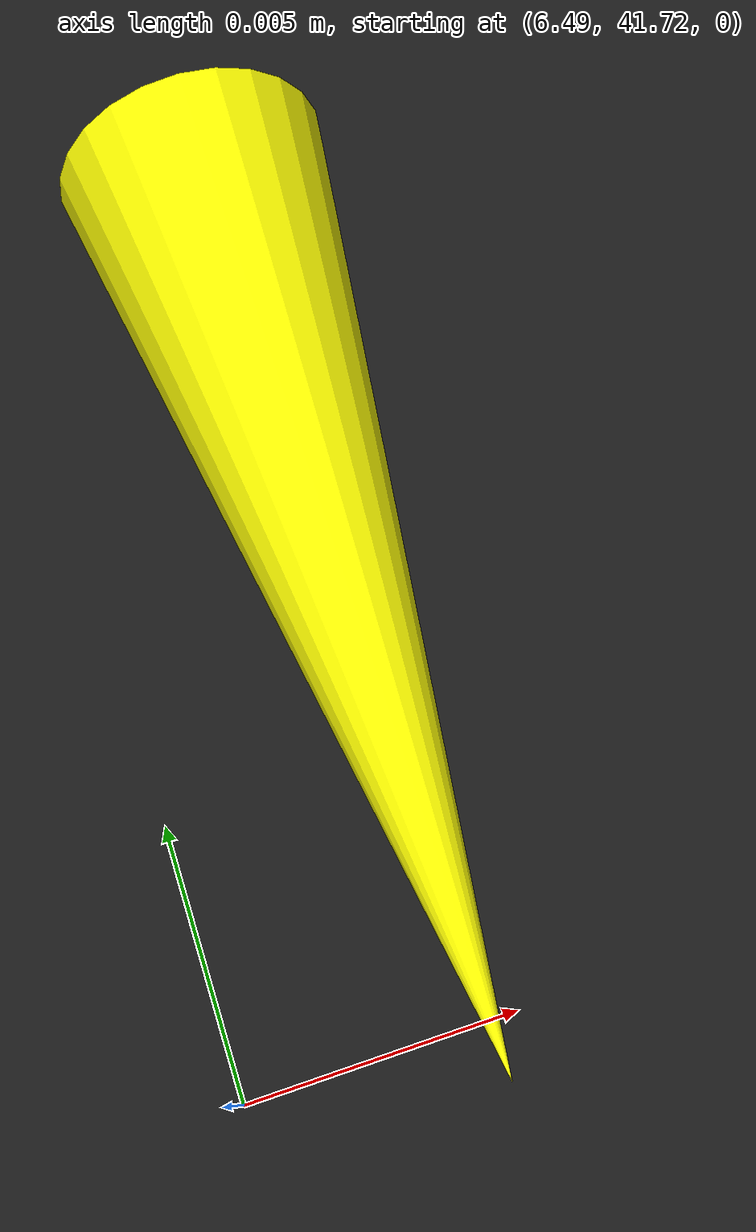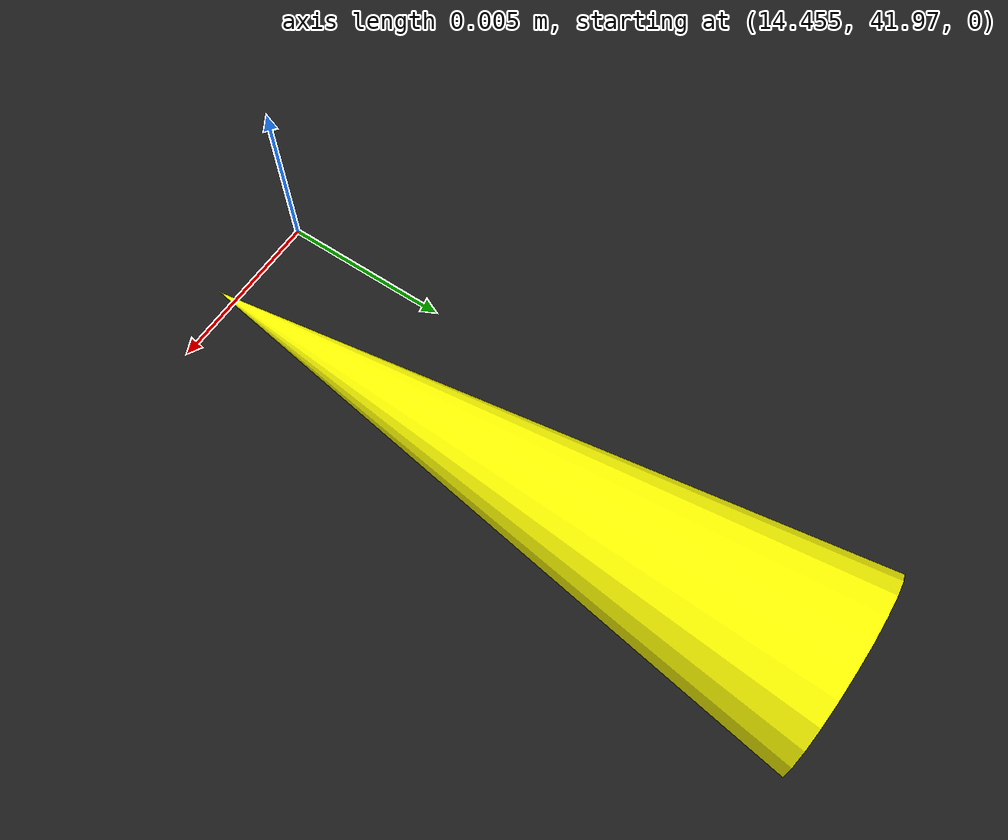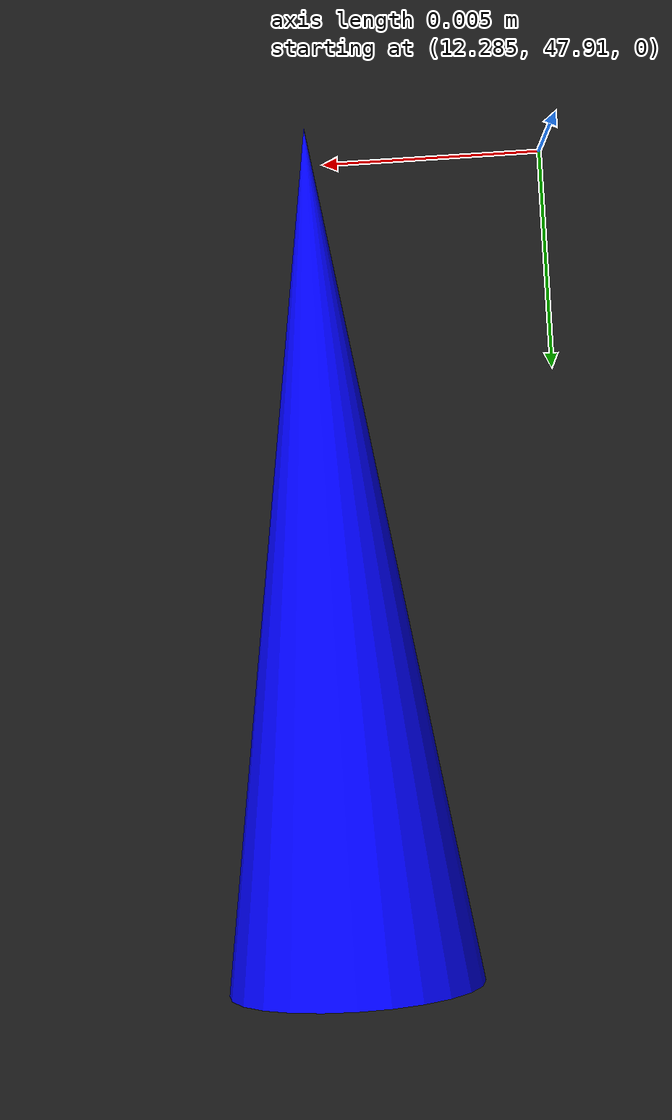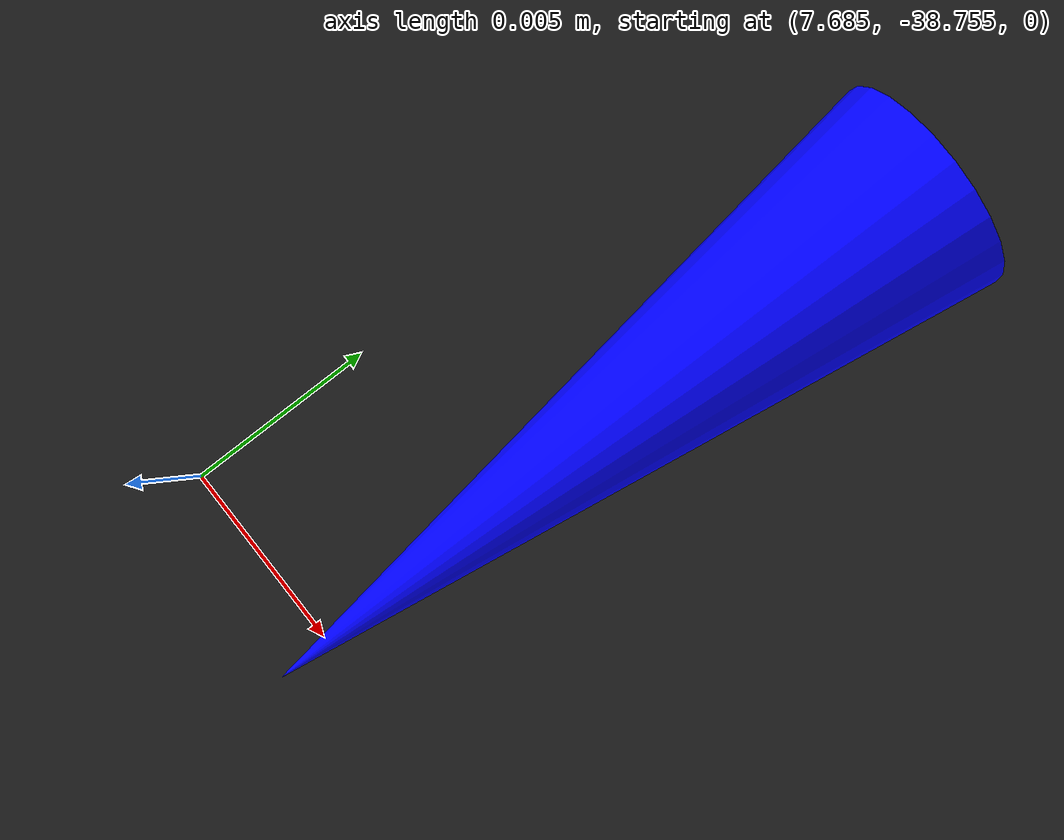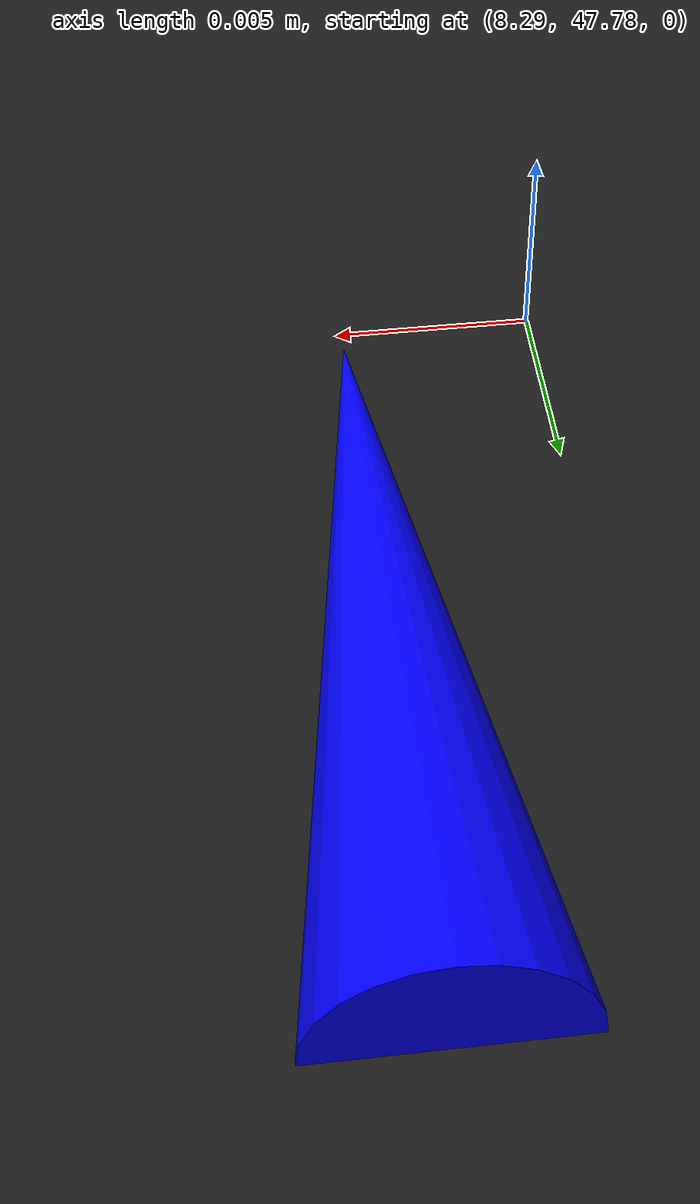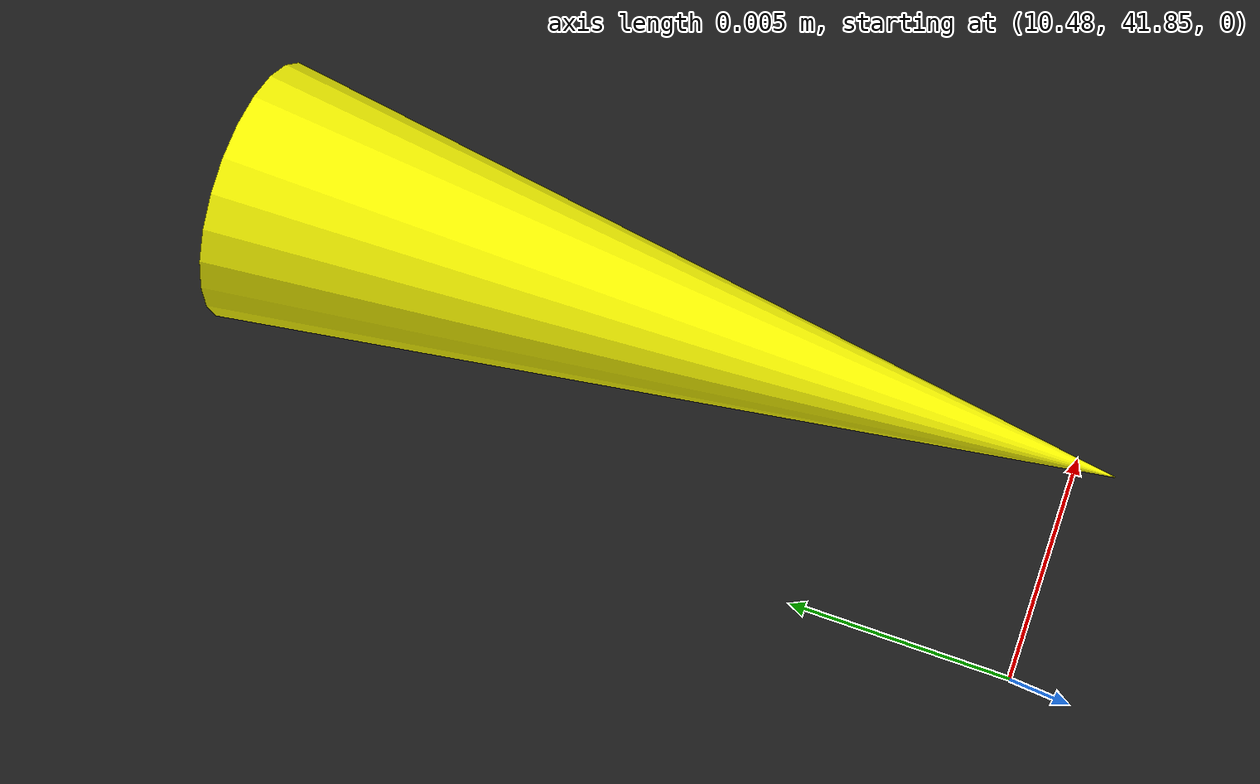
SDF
<?xml version="1.0"?>

<sdf version='1.9'>
    <world name='track'>

        <!-- PHYSICS -->
        <physics name="1ms" type="ignored">
            <max_step_size>0.001</max_step_size>
            <real_time_factor>1.0</real_time_factor>
        </physics>

        <gravity>0 0 -9.8</gravity>
        <magnetic_field>6e-06 2.3e-05 -4.2e-05</magnetic_field>
        <atmosphere type='adiabatic'/>

        <!-- PLUGINS -->
        <plugin name='gz::sim::systems::Physics' filename='gz-sim-physics-system'/>
        <plugin name='gz::sim::systems::UserCommands' filename='gz-sim-user-commands-system'/>
        <plugin name='gz::sim::systems::SceneBroadcaster' filename='gz-sim-scene-broadcaster-system'/>

        <gui fullscreen='0'>
            <!-- 3D scene -->
            <plugin filename="MinimalScene" name="3D View">
                <gz-gui>
                <title>3D View</title>
                <property type="bool" key="showTitleBar">false</property>
                <property type="string" key="state">docked</property>
                </gz-gui>

                <engine>ogre2</engine>
                <scene>scene</scene>
                <ambient_light>0.4 0.4 0.4</ambient_light>
                <background_color>0.8 0.8 0.8</background_color>
                <camera_pose>-6 0 6 0 0.5 0</camera_pose>
            </plugin>

            <!-- Plugins that add functionality to the scene -->
            <plugin filename="EntityContextMenuPlugin" name="Entity context menu">
                <gz-gui>
                <property key="state" type="string">floating</property>
                <property key="width" type="double">5</property>
                <property key="height" type="double">5</property>
                <property key="showTitleBar" type="bool">false</property>
                </gz-gui>
            </plugin>
            <plugin filename="GzSceneManager" name="Scene Manager">
                <gz-gui>
                <property key="resizable" type="bool">false</property>
                <property key="width" type="double">5</property>
                <property key="height" type="double">5</property>
                <property key="state" type="string">floating</property>
                <property key="showTitleBar" type="bool">false</property>
                </gz-gui>
            </plugin>
            <plugin filename="InteractiveViewControl" name="Interactive view control">
                <gz-gui>
                <property key="resizable" type="bool">false</property>
                <property key="width" type="double">5</property>
                <property key="height" type="double">5</property>
                <property key="state" type="string">floating</property>
                <property key="showTitleBar" type="bool">false</property>
                </gz-gui>
            </plugin>
            <plugin filename="CameraTracking" name="Camera Tracking">
                <gz-gui>
                <property key="resizable" type="bool">false</property>
                <property key="width" type="double">5</property>
                <property key="height" type="double">5</property>
                <property key="state" type="string">floating</property>
                <property key="showTitleBar" type="bool">false</property>
                </gz-gui>
            </plugin>
            <plugin name='World control' filename='WorldControl'>
                <gz-gui>
                    <title>World control</title>
                    <property type='bool' key='showTitleBar'>0</property>
                    <property type='bool' key='resizable'>0</property>
                    <property type='double' key='height'>72</property>
                    <property type='double' key='z'>1</property>
                    <property type='string' key='state'>floating</property>
                    <anchors target='3D View'>
                        <line own='left' target='left'/>
                        <line own='bottom' target='bottom'/>
                    </anchors>
                </gz-gui>
                <play_pause>1</play_pause>
                <step>1</step>
                <start_paused>1</start_paused>
            </plugin>
            <plugin name='World stats' filename='WorldStats'>
                <gz-gui>
                    <title>World stats</title>
                    <property type='bool' key='showTitleBar'>0</property>
                    <property type='bool' key='resizable'>0</property>
                    <property type='double' key='height'>110</property>
                    <property type='double' key='width'>290</property>
                    <property type='double' key='z'>1</property>
                    <property type='string' key='state'>floating</property>
                    <anchors target='3D View'>
                        <line own='right' target='right'/>
                        <line own='bottom' target='bottom'/>
                    </anchors>
                </gz-gui>
                <sim_time>1</sim_time>
                <real_time>1</real_time>
                <real_time_factor>1</real_time_factor>
                <iterations>1</iterations>
            </plugin>

            <plugin filename="VisualizeLidar" name="Visualize Lidar">
            </plugin>

            <plugin filename="ImageDisplay" name="Image Display">
            </plugin>

            <!-- Inspector -->
            <plugin filename="ComponentInspector" name="Component inspector">
                <ignition-gui>
                <property type="string" key="state">docked</property>
                </ignition-gui>
            </plugin>

            <!-- Entity tree -->
            <plugin filename="EntityTree" name="Entity tree">
                <ignition-gui>
                <property type="string" key="state">docked</property>
                </ignition-gui>
            </plugin>
        </gui>

        <!-- SENSORS -->

        <plugin
        filename="gz-sim-sensors-system"
        name="gz::sim::systems::Sensors">
        <render_engine>ogre2</render_engine>
        </plugin>

        <!-- AMBIENT -->

        <scene>
            <ambient>1 1 1 1</ambient>
            <background>0.8 0.8 0.8 1</background>
            <shadows>1</shadows>
        </scene>
        <light name='sun' type='directional'>
            <cast_shadows>1</cast_shadows>
            <pose>0 0 10 0 0 0</pose>
            <diffuse>0.8 0.8 0.8 1</diffuse>
            <specular>0.8 0.8 0.8 1</specular>
            <attenuation>
                <range>1000</range>
                <constant>0.9</constant>
                <linear>0.01</linear>
                <quadratic>0.001</quadratic>
            </attenuation>
            <direction>-0.5 0.1 -0.9</direction>
        </light>

        <model name='ground_plane'>
            <static>true</static>
            <link name='link'>
                <collision name='collision'>
                    <geometry>
                        <plane>
                        <normal>0 0 1</normal>
                        <size>100 100</size>
                        </plane>
                    </geometry>

                    <surface>
                        <friction>
                            <dart/>
                        </friction>
                        <bounce/>
                        <contact/>
                    </surface>
                </collision>

                <visual name='visual'>
                    <geometry>
                        <plane>
                        <normal>0 0 1</normal>
                        <size>100 100</size>
                        </plane>
                    </geometry>
                    <material>
                        <ambient>0.1 0.1 0.1 1</ambient>
                        <diffuse>0.1 0.1 0.1 1</diffuse>
                        <specular>0.8 0.8 0.8 1</specular>
                    </material>
                </visual>

                <pose>0 0 0 0 -0 0</pose>

                <inertial>
                    <pose>0 0 0 0 -0 0</pose>
                    <mass>1</mass>
                    <inertia>
                        <ixx>1</ixx>
                        <ixy>0</ixy>
                        <ixz>0</ixz>
                        <iyy>1</iyy>
                        <iyz>0</iyz>
                        <izz>1</izz>
                    </inertia>
                </inertial>

                <enable_wind>false</enable_wind>

            </link>

            <pose>0 0 0 0 -0 0</pose>

            <self_collide>false</self_collide>
        </model>

        <!-- TRACK -->
        <model name='cones'>
            <pose>0 0 0 0 0 0</pose>

      <link name='cone_0_link'>
        <collision name='cone_0_collision'>
          <geometry>
            <mesh>
              <uri>/home/ubuntu/psd_ws/src/psd_gazebo_worlds/world/models/cone/meshes/cone.stl</uri>
              <scale>0.001 0.001 0.001</scale>
            </mesh>
          </geometry>
        </collision>
        <visual name='cone_0_visual'>
          <geometry>
            <mesh>
              <uri>/home/ubuntu/psd_ws/src/psd_gazebo_worlds/world/models/cone/meshes/cone.stl</uri>
              <scale>0.001 0.001 0.001</scale>
            </mesh>
          </geometry>
          <material>
            <ambient>1 1 0 1</ambient>
            <diffuse>1 1 0 1</diffuse>
            <specular>1 1 0 1</specular>
          </material>
        </visual>
        <pose>6.49447171658257 41.7389113024907 0.0 1.57 0 0</pose>
        <enable_wind>false</enable_wind>
      </link>

      <link name='cone_1_link'>
        <collision name='cone_1_collision'>
          <geometry>
            <mesh>
              <uri>/home/ubuntu/psd_ws/src/psd_gazebo_worlds/world/models/cone/meshes/cone.stl</uri>
              <scale>0.001 0.001 0.001</scale>
            </mesh>
          </geometry>
        </collision>
        <visual name='cone_1_visual'>
          <geometry>
            <mesh>
              <uri>/home/ubuntu/psd_ws/src/psd_gazebo_worlds/world/models/cone/meshes/cone.stl</uri>
              <scale>0.001 0.001 0.001</scale>
            </mesh>
          </geometry>
          <material>
            <ambient>1 1 0 1</ambient>
            <diffuse>1 1 0 1</diffuse>
            <specular>1 1 0 1</specular>
          </material>
        </visual>
        <pose>10.4848751821667 41.8690573815958 0.0 1.57 0 0</pose>
        <enable_wind>false</enable_wind>
      </link>

      <link name='cone_2_link'>
        <collision name='cone_2_collision'>
          <geometry>
            <mesh>
              <uri>/home/ubuntu/psd_ws/src/psd_gazebo_worlds/world/models/cone/meshes/cone.stl</uri>
              <scale>0.001 0.001 0.001</scale>
            </mesh>
          </geometry>
        </collision>
        <visual name='cone_2_visual'>
          <geometry>
            <mesh>
              <uri>/home/ubuntu/psd_ws/src/psd_gazebo_worlds/world/models/cone/meshes/cone.stl</uri>
              <scale>0.001 0.001 0.001</scale>
            </mesh>
          </geometry>
          <material>
            <ambient>1 1 0 1</ambient>
            <diffuse>1 1 0 1</diffuse>
            <specular>1 1 0 1</specular>
          </material>
        </visual>
        <pose>14.4579005366844 41.9894100214277 0.0 1.57 0 0</pose>
        <enable_wind>false</enable_wind>
      </link>

      <link name='cone_3_link'>
        <collision name='cone_3_collision'>
          <geometry>
            <mesh>
              <uri>/home/ubuntu/psd_ws/src/psd_gazebo_worlds/world/models/cone/meshes/cone.stl</uri>
              <scale>0.001 0.001 0.001</scale>
            </mesh>
          </geometry>
        </collision>
        <visual name='cone_3_visual'>
          <geometry>
            <mesh>
              <uri>/home/ubuntu/psd_ws/src/psd_gazebo_worlds/world/models/cone/meshes/cone.stl</uri>
              <scale>0.001 0.001 0.001</scale>
            </mesh>
          </geometry>
          <material>
            <ambient>1 1 0 1</ambient>
            <diffuse>1 1 0 1</diffuse>
            <specular>1 1 0 1</specular>
          </material>
        </visual>
        <pose>22.3534294484539 42.1081444836209 0.0 1.57 0 0</pose>
        <enable_wind>false</enable_wind>
      </link>

      <link name='cone_4_link'>
        <collision name='cone_4_collision'>
          <geometry>
            <mesh>
              <uri>/home/ubuntu/psd_ws/src/psd_gazebo_worlds/world/models/cone/meshes/cone.stl</uri>
              <scale>0.001 0.001 0.001</scale>
            </mesh>
          </geometry>
        </collision>
        <visual name='cone_4_visual'>
          <geometry>
            <mesh>
              <uri>/home/ubuntu/psd_ws/src/psd_gazebo_worlds/world/models/cone/meshes/cone.stl</uri>
              <scale>0.001 0.001 0.001</scale>
            </mesh>
          </geometry>
          <material>
            <ambient>1 1 0 1</ambient>
            <diffuse>1 1 0 1</diffuse>
            <specular>1 1 0 1</specular>
          </material>
        </visual>
        <pose>26.2748937812757 42.0609961552005 0.0 1.57 0 0</pose>
        <enable_wind>false</enable_wind>
      </link>

      <link name='cone_5_link'>
        <collision name='cone_5_collision'>
          <geometry>
            <mesh>
              <uri>/home/ubuntu/psd_ws/src/psd_gazebo_worlds/world/models/cone/meshes/cone.stl</uri>
              <scale>0.001 0.001 0.001</scale>
            </mesh>
          </geometry>
        </collision>
        <visual name='cone_5_visual'>
          <geometry>
            <mesh>
              <uri>/home/ubuntu/psd_ws/src/psd_gazebo_worlds/world/models/cone/meshes/cone.stl</uri>
              <scale>0.001 0.001 0.001</scale>
            </mesh>
          </geometry>
          <material>
            <ambient>1 1 0 1</ambient>
            <diffuse>1 1 0 1</diffuse>
            <specular>1 1 0 1</specular>
          </material>
        </visual>
        <pose>30.1761149294924 41.9130441723441 0.0 1.57 0 0</pose>
        <enable_wind>false</enable_wind>
      </link>

      <link name='cone_6_link'>
        <collision name='cone_6_collision'>
          <geometry>
            <mesh>
              <uri>/home/ubuntu/psd_ws/src/psd_gazebo_worlds/world/models/cone/meshes/cone.stl</uri>
              <scale>0.001 0.001 0.001</scale>
            </mesh>
          </geometry>
        </collision>
        <visual name='cone_6_visual'>
          <geometry>
            <mesh>
              <uri>/home/ubuntu/psd_ws/src/psd_gazebo_worlds/world/models/cone/meshes/cone.stl</uri>
              <scale>0.001 0.001 0.001</scale>
            </mesh>
          </geometry>
          <material>
            <ambient>1 1 0 1</ambient>
            <diffuse>1 1 0 1</diffuse>
            <specular>1 1 0 1</specular>
          </material>
        </visual>
        <pose>33.88171993278 41.5914171121172 0.0 1.57 0 0</pose>
        <enable_wind>false</enable_wind>
      </link>

      <link name='cone_7_link'>
        <collision name='cone_7_collision'>
          <geometry>
            <mesh>
              <uri>/home/ubuntu/psd_ws/src/psd_gazebo_worlds/world/models/cone/meshes/cone.stl</uri>
              <scale>0.001 0.001 0.001</scale>
            </mesh>
          </geometry>
        </collision>
        <visual name='cone_7_visual'>
          <geometry>
            <mesh>
              <uri>/home/ubuntu/psd_ws/src/psd_gazebo_worlds/world/models/cone/meshes/cone.stl</uri>
              <scale>0.001 0.001 0.001</scale>
            </mesh>
          </geometry>
          <material>
            <ambient>1 1 0 1</ambient>
            <diffuse>1 1 0 1</diffuse>
            <specular>1 1 0 1</specular>
          </material>
        </visual>
        <pose>38.5108000329817 40.1631834270328 0.0 1.57 0 0</pose>
        <enable_wind>false</enable_wind>
      </link>

      <link name='cone_8_link'>
        <collision name='cone_8_collision'>
          <geometry>
            <mesh>
              <uri>/home/ubuntu/psd_ws/src/psd_gazebo_worlds/world/models/cone/meshes/cone.stl</uri>
              <scale>0.001 0.001 0.001</scale>
            </mesh>
          </geometry>
        </collision>
        <visual name='cone_8_visual'>
          <geometry>
            <mesh>
              <uri>/home/ubuntu/psd_ws/src/psd_gazebo_worlds/world/models/cone/meshes/cone.stl</uri>
              <scale>0.001 0.001 0.001</scale>
            </mesh>
          </geometry>
          <material>
            <ambient>1 1 0 1</ambient>
            <diffuse>1 1 0 1</diffuse>
            <specular>1 1 0 1</specular>
          </material>
        </visual>
        <pose>41.6428012725483 37.057274095852 0.0 1.57 0 0</pose>
        <enable_wind>false</enable_wind>
      </link>

      <link name='cone_9_link'>
        <collision name='cone_9_collision'>
          <geometry>
            <mesh>
              <uri>/home/ubuntu/psd_ws/src/psd_gazebo_worlds/world/models/cone/meshes/cone.stl</uri>
              <scale>0.001 0.001 0.001</scale>
            </mesh>
          </geometry>
        </collision>
        <visual name='cone_9_visual'>
          <geometry>
            <mesh>
              <uri>/home/ubuntu/psd_ws/src/psd_gazebo_worlds/world/models/cone/meshes/cone.stl</uri>
              <scale>0.001 0.001 0.001</scale>
            </mesh>
          </geometry>
          <material>
            <ambient>1 1 0 1</ambient>
            <diffuse>1 1 0 1</diffuse>
            <specular>1 1 0 1</specular>
          </material>
        </visual>
        <pose>42.923741279885 34.1220862330776 0.0 1.57 0 0</pose>
        <enable_wind>false</enable_wind>
      </link>

      <link name='cone_10_link'>
        <collision name='cone_10_collision'>
          <geometry>
            <mesh>
              <uri>/home/ubuntu/psd_ws/src/psd_gazebo_worlds/world/models/cone/meshes/cone.stl</uri>
              <scale>0.001 0.001 0.001</scale>
            </mesh>
          </geometry>
        </collision>
        <visual name='cone_10_visual'>
          <geometry>
            <mesh>
              <uri>/home/ubuntu/psd_ws/src/psd_gazebo_worlds/world/models/cone/meshes/cone.stl</uri>
              <scale>0.001 0.001 0.001</scale>
            </mesh>
          </geometry>
          <material>
            <ambient>1 1 0 1</ambient>
            <diffuse>1 1 0 1</diffuse>
            <specular>1 1 0 1</specular>
          </material>
        </visual>
        <pose>43.4041825643156 29.3682424552239 0.0 1.57 0 0</pose>
        <enable_wind>false</enable_wind>
      </link>

      <link name='cone_11_link'>
        <collision name='cone_11_collision'>
          <geometry>
            <mesh>
              <uri>/home/ubuntu/psd_ws/src/psd_gazebo_worlds/world/models/cone/meshes/cone.stl</uri>
              <scale>0.001 0.001 0.001</scale>
            </mesh>
          </geometry>
        </collision>
        <visual name='cone_11_visual'>
          <geometry>
            <mesh>
              <uri>/home/ubuntu/psd_ws/src/psd_gazebo_worlds/world/models/cone/meshes/cone.stl</uri>
              <scale>0.001 0.001 0.001</scale>
            </mesh>
          </geometry>
          <material>
            <ambient>1 1 0 1</ambient>
            <diffuse>1 1 0 1</diffuse>
            <specular>1 1 0 1</specular>
          </material>
        </visual>
        <pose>42.6373380962399 26.4081334491868 0.0 1.57 0 0</pose>
        <enable_wind>false</enable_wind>
      </link>

      <link name='cone_12_link'>
        <collision name='cone_12_collision'>
          <geometry>
            <mesh>
              <uri>/home/ubuntu/psd_ws/src/psd_gazebo_worlds/world/models/cone/meshes/cone.stl</uri>
              <scale>0.001 0.001 0.001</scale>
            </mesh>
          </geometry>
        </collision>
        <visual name='cone_12_visual'>
          <geometry>
            <mesh>
              <uri>/home/ubuntu/psd_ws/src/psd_gazebo_worlds/world/models/cone/meshes/cone.stl</uri>
              <scale>0.001 0.001 0.001</scale>
            </mesh>
          </geometry>
          <material>
            <ambient>1 1 0 1</ambient>
            <diffuse>1 1 0 1</diffuse>
            <specular>1 1 0 1</specular>
          </material>
        </visual>
        <pose>39.8493389129556 22.6733478226331 0.0 1.57 0 0</pose>
        <enable_wind>false</enable_wind>
      </link>

      <link name='cone_13_link'>
        <collision name='cone_13_collision'>
          <geometry>
            <mesh>
              <uri>/home/ubuntu/psd_ws/src/psd_gazebo_worlds/world/models/cone/meshes/cone.stl</uri>
              <scale>0.001 0.001 0.001</scale>
            </mesh>
          </geometry>
        </collision>
        <visual name='cone_13_visual'>
          <geometry>
            <mesh>
              <uri>/home/ubuntu/psd_ws/src/psd_gazebo_worlds/world/models/cone/meshes/cone.stl</uri>
              <scale>0.001 0.001 0.001</scale>
            </mesh>
          </geometry>
          <material>
            <ambient>1 1 0 1</ambient>
            <diffuse>1 1 0 1</diffuse>
            <specular>1 1 0 1</specular>
          </material>
        </visual>
        <pose>35.6438750732877 19.9947555768891 0.0 1.57 0 0</pose>
        <enable_wind>false</enable_wind>
      </link>

      <link name='cone_14_link'>
        <collision name='cone_14_collision'>
          <geometry>
            <mesh>
              <uri>/home/ubuntu/psd_ws/src/psd_gazebo_worlds/world/models/cone/meshes/cone.stl</uri>
              <scale>0.001 0.001 0.001</scale>
            </mesh>
          </geometry>
        </collision>
        <visual name='cone_14_visual'>
          <geometry>
            <mesh>
              <uri>/home/ubuntu/psd_ws/src/psd_gazebo_worlds/world/models/cone/meshes/cone.stl</uri>
              <scale>0.001 0.001 0.001</scale>
            </mesh>
          </geometry>
          <material>
            <ambient>1 1 0 1</ambient>
            <diffuse>1 1 0 1</diffuse>
            <specular>1 1 0 1</specular>
          </material>
        </visual>
        <pose>32.5117013027651 19.0709696852617 0.0 1.57 0 0</pose>
        <enable_wind>false</enable_wind>
      </link>

      <link name='cone_15_link'>
        <collision name='cone_15_collision'>
          <geometry>
            <mesh>
              <uri>/home/ubuntu/psd_ws/src/psd_gazebo_worlds/world/models/cone/meshes/cone.stl</uri>
              <scale>0.001 0.001 0.001</scale>
            </mesh>
          </geometry>
        </collision>
        <visual name='cone_15_visual'>
          <geometry>
            <mesh>
              <uri>/home/ubuntu/psd_ws/src/psd_gazebo_worlds/world/models/cone/meshes/cone.stl</uri>
              <scale>0.001 0.001 0.001</scale>
            </mesh>
          </geometry>
          <material>
            <ambient>1 1 0 1</ambient>
            <diffuse>1 1 0 1</diffuse>
            <specular>1 1 0 1</specular>
          </material>
        </visual>
        <pose>29.305019764528 18.9545691109581 0.0 1.57 0 0</pose>
        <enable_wind>false</enable_wind>
      </link>

      <link name='cone_16_link'>
        <collision name='cone_16_collision'>
          <geometry>
            <mesh>
              <uri>/home/ubuntu/psd_ws/src/psd_gazebo_worlds/world/models/cone/meshes/cone.stl</uri>
              <scale>0.001 0.001 0.001</scale>
            </mesh>
          </geometry>
        </collision>
        <visual name='cone_16_visual'>
          <geometry>
            <mesh>
              <uri>/home/ubuntu/psd_ws/src/psd_gazebo_worlds/world/models/cone/meshes/cone.stl</uri>
              <scale>0.001 0.001 0.001</scale>
            </mesh>
          </geometry>
          <material>
            <ambient>1 1 0 1</ambient>
            <diffuse>1 1 0 1</diffuse>
            <specular>1 1 0 1</specular>
          </material>
        </visual>
        <pose>24.4759113345748 20.2570787967781 0.0 1.57 0 0</pose>
        <enable_wind>false</enable_wind>
      </link>

      <link name='cone_17_link'>
        <collision name='cone_17_collision'>
          <geometry>
            <mesh>
              <uri>/home/ubuntu/psd_ws/src/psd_gazebo_worlds/world/models/cone/meshes/cone.stl</uri>
              <scale>0.001 0.001 0.001</scale>
            </mesh>
          </geometry>
        </collision>
        <visual name='cone_17_visual'>
          <geometry>
            <mesh>
              <uri>/home/ubuntu/psd_ws/src/psd_gazebo_worlds/world/models/cone/meshes/cone.stl</uri>
              <scale>0.001 0.001 0.001</scale>
            </mesh>
          </geometry>
          <material>
            <ambient>1 1 0 1</ambient>
            <diffuse>1 1 0 1</diffuse>
            <specular>1 1 0 1</specular>
          </material>
        </visual>
        <pose>19.8072187451783 22.9775182612717 0.0 1.57 0 0</pose>
        <enable_wind>false</enable_wind>
      </link>

      <link name='cone_18_link'>
        <collision name='cone_18_collision'>
          <geometry>
            <mesh>
              <uri>/home/ubuntu/psd_ws/src/psd_gazebo_worlds/world/models/cone/meshes/cone.stl</uri>
              <scale>0.001 0.001 0.001</scale>
            </mesh>
          </geometry>
        </collision>
        <visual name='cone_18_visual'>
          <geometry>
            <mesh>
              <uri>/home/ubuntu/psd_ws/src/psd_gazebo_worlds/world/models/cone/meshes/cone.stl</uri>
              <scale>0.001 0.001 0.001</scale>
            </mesh>
          </geometry>
          <material>
            <ambient>1 1 0 1</ambient>
            <diffuse>1 1 0 1</diffuse>
            <specular>1 1 0 1</specular>
          </material>
        </visual>
        <pose>16.5291821840059 25.277806927272 0.0 1.57 0 0</pose>
        <enable_wind>false</enable_wind>
      </link>

      <link name='cone_19_link'>
        <collision name='cone_19_collision'>
          <geometry>
            <mesh>
              <uri>/home/ubuntu/psd_ws/src/psd_gazebo_worlds/world/models/cone/meshes/cone.stl</uri>
              <scale>0.001 0.001 0.001</scale>
            </mesh>
          </geometry>
        </collision>
        <visual name='cone_19_visual'>
          <geometry>
            <mesh>
              <uri>/home/ubuntu/psd_ws/src/psd_gazebo_worlds/world/models/cone/meshes/cone.stl</uri>
              <scale>0.001 0.001 0.001</scale>
            </mesh>
          </geometry>
          <material>
            <ambient>1 1 0 1</ambient>
            <diffuse>1 1 0 1</diffuse>
            <specular>1 1 0 1</specular>
          </material>
        </visual>
        <pose>10.7566166245341 28.5122919557571 0.0 1.57 0 0</pose>
        <enable_wind>false</enable_wind>
      </link>

      <link name='cone_20_link'>
        <collision name='cone_20_collision'>
          <geometry>
            <mesh>
              <uri>/home/ubuntu/psd_ws/src/psd_gazebo_worlds/world/models/cone/meshes/cone.stl</uri>
              <scale>0.001 0.001 0.001</scale>
            </mesh>
          </geometry>
        </collision>
        <visual name='cone_20_visual'>
          <geometry>
            <mesh>
              <uri>/home/ubuntu/psd_ws/src/psd_gazebo_worlds/world/models/cone/meshes/cone.stl</uri>
              <scale>0.001 0.001 0.001</scale>
            </mesh>
          </geometry>
          <material>
            <ambient>1 1 0 1</ambient>
            <diffuse>1 1 0 1</diffuse>
            <specular>1 1 0 1</specular>
          </material>
        </visual>
        <pose>6.36970146209175 29.8034933598624 0.0 1.57 0 0</pose>
        <enable_wind>false</enable_wind>
      </link>

      <link name='cone_21_link'>
        <collision name='cone_21_collision'>
          <geometry>
            <mesh>
              <uri>/home/ubuntu/psd_ws/src/psd_gazebo_worlds/world/models/cone/meshes/cone.stl</uri>
              <scale>0.001 0.001 0.001</scale>
            </mesh>
          </geometry>
        </collision>
        <visual name='cone_21_visual'>
          <geometry>
            <mesh>
              <uri>/home/ubuntu/psd_ws/src/psd_gazebo_worlds/world/models/cone/meshes/cone.stl</uri>
              <scale>0.001 0.001 0.001</scale>
            </mesh>
          </geometry>
          <material>
            <ambient>1 1 0 1</ambient>
            <diffuse>1 1 0 1</diffuse>
            <specular>1 1 0 1</specular>
          </material>
        </visual>
        <pose>-0.405973075502234 30.1500578730274 0.0 1.57 0 0</pose>
        <enable_wind>false</enable_wind>
      </link>

      <link name='cone_22_link'>
        <collision name='cone_22_collision'>
          <geometry>
            <mesh>
              <uri>/home/ubuntu/psd_ws/src/psd_gazebo_worlds/world/models/cone/meshes/cone.stl</uri>
              <scale>0.001 0.001 0.001</scale>
            </mesh>
          </geometry>
        </collision>
        <visual name='cone_22_visual'>
          <geometry>
            <mesh>
              <uri>/home/ubuntu/psd_ws/src/psd_gazebo_worlds/world/models/cone/meshes/cone.stl</uri>
              <scale>0.001 0.001 0.001</scale>
            </mesh>
          </geometry>
          <material>
            <ambient>1 1 0 1</ambient>
            <diffuse>1 1 0 1</diffuse>
            <specular>1 1 0 1</specular>
          </material>
        </visual>
        <pose>-7.53032772904185 27.7630095130657 0.0 1.57 0 0</pose>
        <enable_wind>false</enable_wind>
      </link>

      <link name='cone_23_link'>
        <collision name='cone_23_collision'>
          <geometry>
            <mesh>
              <uri>/home/ubuntu/psd_ws/src/psd_gazebo_worlds/world/models/cone/meshes/cone.stl</uri>
              <scale>0.001 0.001 0.001</scale>
            </mesh>
          </geometry>
        </collision>
        <visual name='cone_23_visual'>
          <geometry>
            <mesh>
              <uri>/home/ubuntu/psd_ws/src/psd_gazebo_worlds/world/models/cone/meshes/cone.stl</uri>
              <scale>0.001 0.001 0.001</scale>
            </mesh>
          </geometry>
          <material>
            <ambient>1 1 0 1</ambient>
            <diffuse>1 1 0 1</diffuse>
            <specular>1 1 0 1</specular>
          </material>
        </visual>
        <pose>-10.9967405848897 23.4446538263345 0.0 1.57 0 0</pose>
        <enable_wind>false</enable_wind>
      </link>

      <link name='cone_24_link'>
        <collision name='cone_24_collision'>
          <geometry>
            <mesh>
              <uri>/home/ubuntu/psd_ws/src/psd_gazebo_worlds/world/models/cone/meshes/cone.stl</uri>
              <scale>0.001 0.001 0.001</scale>
            </mesh>
          </geometry>
        </collision>
        <visual name='cone_24_visual'>
          <geometry>
            <mesh>
              <uri>/home/ubuntu/psd_ws/src/psd_gazebo_worlds/world/models/cone/meshes/cone.stl</uri>
              <scale>0.001 0.001 0.001</scale>
            </mesh>
          </geometry>
          <material>
            <ambient>1 1 0 1</ambient>
            <diffuse>1 1 0 1</diffuse>
            <specular>1 1 0 1</specular>
          </material>
        </visual>
        <pose>-11.7945553145768 18.0098876247875 0.0 1.57 0 0</pose>
        <enable_wind>false</enable_wind>
      </link>

      <link name='cone_25_link'>
        <collision name='cone_25_collision'>
          <geometry>
            <mesh>
              <uri>/home/ubuntu/psd_ws/src/psd_gazebo_worlds/world/models/cone/meshes/cone.stl</uri>
              <scale>0.001 0.001 0.001</scale>
            </mesh>
          </geometry>
        </collision>
        <visual name='cone_25_visual'>
          <geometry>
            <mesh>
              <uri>/home/ubuntu/psd_ws/src/psd_gazebo_worlds/world/models/cone/meshes/cone.stl</uri>
              <scale>0.001 0.001 0.001</scale>
            </mesh>
          </geometry>
          <material>
            <ambient>1 1 0 1</ambient>
            <diffuse>1 1 0 1</diffuse>
            <specular>1 1 0 1</specular>
          </material>
        </visual>
        <pose>-9.84329815385971 12.9293912425976 0.0 1.57 0 0</pose>
        <enable_wind>false</enable_wind>
      </link>

      <link name='cone_26_link'>
        <collision name='cone_26_collision'>
          <geometry>
            <mesh>
              <uri>/home/ubuntu/psd_ws/src/psd_gazebo_worlds/world/models/cone/meshes/cone.stl</uri>
              <scale>0.001 0.001 0.001</scale>
            </mesh>
          </geometry>
        </collision>
        <visual name='cone_26_visual'>
          <geometry>
            <mesh>
              <uri>/home/ubuntu/psd_ws/src/psd_gazebo_worlds/world/models/cone/meshes/cone.stl</uri>
              <scale>0.001 0.001 0.001</scale>
            </mesh>
          </geometry>
          <material>
            <ambient>1 1 0 1</ambient>
            <diffuse>1 1 0 1</diffuse>
            <specular>1 1 0 1</specular>
          </material>
        </visual>
        <pose>-2.64821833398598 7.33684919790624 0.0 1.57 0 0</pose>
        <enable_wind>false</enable_wind>
      </link>

      <link name='cone_27_link'>
        <collision name='cone_27_collision'>
          <geometry>
            <mesh>
              <uri>/home/ubuntu/psd_ws/src/psd_gazebo_worlds/world/models/cone/meshes/cone.stl</uri>
              <scale>0.001 0.001 0.001</scale>
            </mesh>
          </geometry>
        </collision>
        <visual name='cone_27_visual'>
          <geometry>
            <mesh>
              <uri>/home/ubuntu/psd_ws/src/psd_gazebo_worlds/world/models/cone/meshes/cone.stl</uri>
              <scale>0.001 0.001 0.001</scale>
            </mesh>
          </geometry>
          <material>
            <ambient>1 1 0 1</ambient>
            <diffuse>1 1 0 1</diffuse>
            <specular>1 1 0 1</specular>
          </material>
        </visual>
        <pose>-0.139159724307982 5.41310565569044 0.0 1.57 0 0</pose>
        <enable_wind>false</enable_wind>
      </link>

      <link name='cone_28_link'>
        <collision name='cone_28_collision'>
          <geometry>
            <mesh>
              <uri>/home/ubuntu/psd_ws/src/psd_gazebo_worlds/world/models/cone/meshes/cone.stl</uri>
              <scale>0.001 0.001 0.001</scale>
            </mesh>
          </geometry>
        </collision>
        <visual name='cone_28_visual'>
          <geometry>
            <mesh>
              <uri>/home/ubuntu/psd_ws/src/psd_gazebo_worlds/world/models/cone/meshes/cone.stl</uri>
              <scale>0.001 0.001 0.001</scale>
            </mesh>
          </geometry>
          <material>
            <ambient>1 1 0 1</ambient>
            <diffuse>1 1 0 1</diffuse>
            <specular>1 1 0 1</specular>
          </material>
        </visual>
        <pose>1.00846697640521 3.25999992647677 0.0 1.57 0 0</pose>
        <enable_wind>false</enable_wind>
      </link>

      <link name='cone_29_link'>
        <collision name='cone_29_collision'>
          <geometry>
            <mesh>
              <uri>/home/ubuntu/psd_ws/src/psd_gazebo_worlds/world/models/cone/meshes/cone.stl</uri>
              <scale>0.001 0.001 0.001</scale>
            </mesh>
          </geometry>
        </collision>
        <visual name='cone_29_visual'>
          <geometry>
            <mesh>
              <uri>/home/ubuntu/psd_ws/src/psd_gazebo_worlds/world/models/cone/meshes/cone.stl</uri>
              <scale>0.001 0.001 0.001</scale>
            </mesh>
          </geometry>
          <material>
            <ambient>1 1 0 1</ambient>
            <diffuse>1 1 0 1</diffuse>
            <specular>1 1 0 1</specular>
          </material>
        </visual>
        <pose>1.7076976610908 -2.501572642794 0.0 1.57 0 0</pose>
        <enable_wind>false</enable_wind>
      </link>

      <link name='cone_30_link'>
        <collision name='cone_30_collision'>
          <geometry>
            <mesh>
              <uri>/home/ubuntu/psd_ws/src/psd_gazebo_worlds/world/models/cone/meshes/cone.stl</uri>
              <scale>0.001 0.001 0.001</scale>
            </mesh>
          </geometry>
        </collision>
        <visual name='cone_30_visual'>
          <geometry>
            <mesh>
              <uri>/home/ubuntu/psd_ws/src/psd_gazebo_worlds/world/models/cone/meshes/cone.stl</uri>
              <scale>0.001 0.001 0.001</scale>
            </mesh>
          </geometry>
          <material>
            <ambient>1 1 0 1</ambient>
            <diffuse>1 1 0 1</diffuse>
            <specular>1 1 0 1</specular>
          </material>
        </visual>
        <pose>5.90118769712182 -9.36241405660719 0.0 1.57 0 0</pose>
        <enable_wind>false</enable_wind>
      </link>

      <link name='cone_31_link'>
        <collision name='cone_31_collision'>
          <geometry>
            <mesh>
              <uri>/home/ubuntu/psd_ws/src/psd_gazebo_worlds/world/models/cone/meshes/cone.stl</uri>
              <scale>0.001 0.001 0.001</scale>
            </mesh>
          </geometry>
        </collision>
        <visual name='cone_31_visual'>
          <geometry>
            <mesh>
              <uri>/home/ubuntu/psd_ws/src/psd_gazebo_worlds/world/models/cone/meshes/cone.stl</uri>
              <scale>0.001 0.001 0.001</scale>
            </mesh>
          </geometry>
          <material>
            <ambient>1 1 0 1</ambient>
            <diffuse>1 1 0 1</diffuse>
            <specular>1 1 0 1</specular>
          </material>
        </visual>
        <pose>10.4108490166236 -11.5249176387577 0.0 1.57 0 0</pose>
        <enable_wind>false</enable_wind>
      </link>

      <link name='cone_32_link'>
        <collision name='cone_32_collision'>
          <geometry>
            <mesh>
              <uri>/home/ubuntu/psd_ws/src/psd_gazebo_worlds/world/models/cone/meshes/cone.stl</uri>
              <scale>0.001 0.001 0.001</scale>
            </mesh>
          </geometry>
        </collision>
        <visual name='cone_32_visual'>
          <geometry>
            <mesh>
              <uri>/home/ubuntu/psd_ws/src/psd_gazebo_worlds/world/models/cone/meshes/cone.stl</uri>
              <scale>0.001 0.001 0.001</scale>
            </mesh>
          </geometry>
          <material>
            <ambient>1 1 0 1</ambient>
            <diffuse>1 1 0 1</diffuse>
            <specular>1 1 0 1</specular>
          </material>
        </visual>
        <pose>16.6611999625517 -12.7135418322201 0.0 1.57 0 0</pose>
        <enable_wind>false</enable_wind>
      </link>

      <link name='cone_33_link'>
        <collision name='cone_33_collision'>
          <geometry>
            <mesh>
              <uri>/home/ubuntu/psd_ws/src/psd_gazebo_worlds/world/models/cone/meshes/cone.stl</uri>
              <scale>0.001 0.001 0.001</scale>
            </mesh>
          </geometry>
        </collision>
        <visual name='cone_33_visual'>
          <geometry>
            <mesh>
              <uri>/home/ubuntu/psd_ws/src/psd_gazebo_worlds/world/models/cone/meshes/cone.stl</uri>
              <scale>0.001 0.001 0.001</scale>
            </mesh>
          </geometry>
          <material>
            <ambient>1 1 0 1</ambient>
            <diffuse>1 1 0 1</diffuse>
            <specular>1 1 0 1</specular>
          </material>
        </visual>
        <pose>20.2513584750154 -13.4902268953088 0.0 1.57 0 0</pose>
        <enable_wind>false</enable_wind>
      </link>

      <link name='cone_34_link'>
        <collision name='cone_34_collision'>
          <geometry>
            <mesh>
              <uri>/home/ubuntu/psd_ws/src/psd_gazebo_worlds/world/models/cone/meshes/cone.stl</uri>
              <scale>0.001 0.001 0.001</scale>
            </mesh>
          </geometry>
        </collision>
        <visual name='cone_34_visual'>
          <geometry>
            <mesh>
              <uri>/home/ubuntu/psd_ws/src/psd_gazebo_worlds/world/models/cone/meshes/cone.stl</uri>
              <scale>0.001 0.001 0.001</scale>
            </mesh>
          </geometry>
          <material>
            <ambient>1 1 0 1</ambient>
            <diffuse>1 1 0 1</diffuse>
            <specular>1 1 0 1</specular>
          </material>
        </visual>
        <pose>23.7938485314227 -14.6351269687361 0.0 1.57 0 0</pose>
        <enable_wind>false</enable_wind>
      </link>

      <link name='cone_35_link'>
        <collision name='cone_35_collision'>
          <geometry>
            <mesh>
              <uri>/home/ubuntu/psd_ws/src/psd_gazebo_worlds/world/models/cone/meshes/cone.stl</uri>
              <scale>0.001 0.001 0.001</scale>
            </mesh>
          </geometry>
        </collision>
        <visual name='cone_35_visual'>
          <geometry>
            <mesh>
              <uri>/home/ubuntu/psd_ws/src/psd_gazebo_worlds/world/models/cone/meshes/cone.stl</uri>
              <scale>0.001 0.001 0.001</scale>
            </mesh>
          </geometry>
          <material>
            <ambient>1 1 0 1</ambient>
            <diffuse>1 1 0 1</diffuse>
            <specular>1 1 0 1</specular>
          </material>
        </visual>
        <pose>30.7681622622371 -17.739262619614 0.0 1.57 0 0</pose>
        <enable_wind>false</enable_wind>
      </link>

      <link name='cone_36_link'>
        <collision name='cone_36_collision'>
          <geometry>
            <mesh>
              <uri>/home/ubuntu/psd_ws/src/psd_gazebo_worlds/world/models/cone/meshes/cone.stl</uri>
              <scale>0.001 0.001 0.001</scale>
            </mesh>
          </geometry>
        </collision>
        <visual name='cone_36_visual'>
          <geometry>
            <mesh>
              <uri>/home/ubuntu/psd_ws/src/psd_gazebo_worlds/world/models/cone/meshes/cone.stl</uri>
              <scale>0.001 0.001 0.001</scale>
            </mesh>
          </geometry>
          <material>
            <ambient>1 1 0 1</ambient>
            <diffuse>1 1 0 1</diffuse>
            <specular>1 1 0 1</specular>
          </material>
        </visual>
        <pose>33.7897740653103 -19.5166383512928 0.0 1.57 0 0</pose>
        <enable_wind>false</enable_wind>
      </link>

      <link name='cone_37_link'>
        <collision name='cone_37_collision'>
          <geometry>
            <mesh>
              <uri>/home/ubuntu/psd_ws/src/psd_gazebo_worlds/world/models/cone/meshes/cone.stl</uri>
              <scale>0.001 0.001 0.001</scale>
            </mesh>
          </geometry>
        </collision>
        <visual name='cone_37_visual'>
          <geometry>
            <mesh>
              <uri>/home/ubuntu/psd_ws/src/psd_gazebo_worlds/world/models/cone/meshes/cone.stl</uri>
              <scale>0.001 0.001 0.001</scale>
            </mesh>
          </geometry>
          <material>
            <ambient>1 1 0 1</ambient>
            <diffuse>1 1 0 1</diffuse>
            <specular>1 1 0 1</specular>
          </material>
        </visual>
        <pose>35.8614855279756 -21.5808775016001 0.0 1.57 0 0</pose>
        <enable_wind>false</enable_wind>
      </link>

      <link name='cone_38_link'>
        <collision name='cone_38_collision'>
          <geometry>
            <mesh>
              <uri>/home/ubuntu/psd_ws/src/psd_gazebo_worlds/world/models/cone/meshes/cone.stl</uri>
              <scale>0.001 0.001 0.001</scale>
            </mesh>
          </geometry>
        </collision>
        <visual name='cone_38_visual'>
          <geometry>
            <mesh>
              <uri>/home/ubuntu/psd_ws/src/psd_gazebo_worlds/world/models/cone/meshes/cone.stl</uri>
              <scale>0.001 0.001 0.001</scale>
            </mesh>
          </geometry>
          <material>
            <ambient>1 1 0 1</ambient>
            <diffuse>1 1 0 1</diffuse>
            <specular>1 1 0 1</specular>
          </material>
        </visual>
        <pose>36.8711477182864 -25.4557910211687 0.0 1.57 0 0</pose>
        <enable_wind>false</enable_wind>
      </link>

      <link name='cone_39_link'>
        <collision name='cone_39_collision'>
          <geometry>
            <mesh>
              <uri>/home/ubuntu/psd_ws/src/psd_gazebo_worlds/world/models/cone/meshes/cone.stl</uri>
              <scale>0.001 0.001 0.001</scale>
            </mesh>
          </geometry>
        </collision>
        <visual name='cone_39_visual'>
          <geometry>
            <mesh>
              <uri>/home/ubuntu/psd_ws/src/psd_gazebo_worlds/world/models/cone/meshes/cone.stl</uri>
              <scale>0.001 0.001 0.001</scale>
            </mesh>
          </geometry>
          <material>
            <ambient>1 1 0 1</ambient>
            <diffuse>1 1 0 1</diffuse>
            <specular>1 1 0 1</specular>
          </material>
        </visual>
        <pose>35.5175477601575 -29.6867414698392 0.0 1.57 0 0</pose>
        <enable_wind>false</enable_wind>
      </link>

      <link name='cone_40_link'>
        <collision name='cone_40_collision'>
          <geometry>
            <mesh>
              <uri>/home/ubuntu/psd_ws/src/psd_gazebo_worlds/world/models/cone/meshes/cone.stl</uri>
              <scale>0.001 0.001 0.001</scale>
            </mesh>
          </geometry>
        </collision>
        <visual name='cone_40_visual'>
          <geometry>
            <mesh>
              <uri>/home/ubuntu/psd_ws/src/psd_gazebo_worlds/world/models/cone/meshes/cone.stl</uri>
              <scale>0.001 0.001 0.001</scale>
            </mesh>
          </geometry>
          <material>
            <ambient>1 1 0 1</ambient>
            <diffuse>1 1 0 1</diffuse>
            <specular>1 1 0 1</specular>
          </material>
        </visual>
        <pose>33.5888282300982 -31.9233335254203 0.0 1.57 0 0</pose>
        <enable_wind>false</enable_wind>
      </link>

      <link name='cone_41_link'>
        <collision name='cone_41_collision'>
          <geometry>
            <mesh>
              <uri>/home/ubuntu/psd_ws/src/psd_gazebo_worlds/world/models/cone/meshes/cone.stl</uri>
              <scale>0.001 0.001 0.001</scale>
            </mesh>
          </geometry>
        </collision>
        <visual name='cone_41_visual'>
          <geometry>
            <mesh>
              <uri>/home/ubuntu/psd_ws/src/psd_gazebo_worlds/world/models/cone/meshes/cone.stl</uri>
              <scale>0.001 0.001 0.001</scale>
            </mesh>
          </geometry>
          <material>
            <ambient>1 1 0 1</ambient>
            <diffuse>1 1 0 1</diffuse>
            <specular>1 1 0 1</specular>
          </material>
        </visual>
        <pose>29.6211021726631 -33.5886007841515 0.0 1.57 0 0</pose>
        <enable_wind>false</enable_wind>
      </link>

      <link name='cone_42_link'>
        <collision name='cone_42_collision'>
          <geometry>
            <mesh>
              <uri>/home/ubuntu/psd_ws/src/psd_gazebo_worlds/world/models/cone/meshes/cone.stl</uri>
              <scale>0.001 0.001 0.001</scale>
            </mesh>
          </geometry>
        </collision>
        <visual name='cone_42_visual'>
          <geometry>
            <mesh>
              <uri>/home/ubuntu/psd_ws/src/psd_gazebo_worlds/world/models/cone/meshes/cone.stl</uri>
              <scale>0.001 0.001 0.001</scale>
            </mesh>
          </geometry>
          <material>
            <ambient>1 1 0 1</ambient>
            <diffuse>1 1 0 1</diffuse>
            <specular>1 1 0 1</specular>
          </material>
        </visual>
        <pose>26.2183096377485 -33.68480226464 0.0 1.57 0 0</pose>
        <enable_wind>false</enable_wind>
      </link>

      <link name='cone_43_link'>
        <collision name='cone_43_collision'>
          <geometry>
            <mesh>
              <uri>/home/ubuntu/psd_ws/src/psd_gazebo_worlds/world/models/cone/meshes/cone.stl</uri>
              <scale>0.001 0.001 0.001</scale>
            </mesh>
          </geometry>
        </collision>
        <visual name='cone_43_visual'>
          <geometry>
            <mesh>
              <uri>/home/ubuntu/psd_ws/src/psd_gazebo_worlds/world/models/cone/meshes/cone.stl</uri>
              <scale>0.001 0.001 0.001</scale>
            </mesh>
          </geometry>
          <material>
            <ambient>1 1 0 1</ambient>
            <diffuse>1 1 0 1</diffuse>
            <specular>1 1 0 1</specular>
          </material>
        </visual>
        <pose>22.3208062313579 -33.3726612899257 0.0 1.57 0 0</pose>
        <enable_wind>false</enable_wind>
      </link>

      <link name='cone_44_link'>
        <collision name='cone_44_collision'>
          <geometry>
            <mesh>
              <uri>/home/ubuntu/psd_ws/src/psd_gazebo_worlds/world/models/cone/meshes/cone.stl</uri>
              <scale>0.001 0.001 0.001</scale>
            </mesh>
          </geometry>
        </collision>
        <visual name='cone_44_visual'>
          <geometry>
            <mesh>
              <uri>/home/ubuntu/psd_ws/src/psd_gazebo_worlds/world/models/cone/meshes/cone.stl</uri>
              <scale>0.001 0.001 0.001</scale>
            </mesh>
          </geometry>
          <material>
            <ambient>1 1 0 1</ambient>
            <diffuse>1 1 0 1</diffuse>
            <specular>1 1 0 1</specular>
          </material>
        </visual>
        <pose>14.1429922166079 -33.1731958647648 0.0 1.57 0 0</pose>
        <enable_wind>false</enable_wind>
      </link>

      <link name='cone_45_link'>
        <collision name='cone_45_collision'>
          <geometry>
            <mesh>
              <uri>/home/ubuntu/psd_ws/src/psd_gazebo_worlds/world/models/cone/meshes/cone.stl</uri>
              <scale>0.001 0.001 0.001</scale>
            </mesh>
          </geometry>
        </collision>
        <visual name='cone_45_visual'>
          <geometry>
            <mesh>
              <uri>/home/ubuntu/psd_ws/src/psd_gazebo_worlds/world/models/cone/meshes/cone.stl</uri>
              <scale>0.001 0.001 0.001</scale>
            </mesh>
          </geometry>
          <material>
            <ambient>1 1 0 1</ambient>
            <diffuse>1 1 0 1</diffuse>
            <specular>1 1 0 1</specular>
          </material>
        </visual>
        <pose>10.3778348140314 -33.0132052855498 0.0 1.57 0 0</pose>
        <enable_wind>false</enable_wind>
      </link>

      <link name='cone_46_link'>
        <collision name='cone_46_collision'>
          <geometry>
            <mesh>
              <uri>/home/ubuntu/psd_ws/src/psd_gazebo_worlds/world/models/cone/meshes/cone.stl</uri>
              <scale>0.001 0.001 0.001</scale>
            </mesh>
          </geometry>
        </collision>
        <visual name='cone_46_visual'>
          <geometry>
            <mesh>
              <uri>/home/ubuntu/psd_ws/src/psd_gazebo_worlds/world/models/cone/meshes/cone.stl</uri>
              <scale>0.001 0.001 0.001</scale>
            </mesh>
          </geometry>
          <material>
            <ambient>1 1 0 1</ambient>
            <diffuse>1 1 0 1</diffuse>
            <specular>1 1 0 1</specular>
          </material>
        </visual>
        <pose>6.84064584789227 -32.4725374962639 0.0 1.57 0 0</pose>
        <enable_wind>false</enable_wind>
      </link>

      <link name='cone_47_link'>
        <collision name='cone_47_collision'>
          <geometry>
            <mesh>
              <uri>/home/ubuntu/psd_ws/src/psd_gazebo_worlds/world/models/cone/meshes/cone.stl</uri>
              <scale>0.001 0.001 0.001</scale>
            </mesh>
          </geometry>
        </collision>
        <visual name='cone_47_visual'>
          <geometry>
            <mesh>
              <uri>/home/ubuntu/psd_ws/src/psd_gazebo_worlds/world/models/cone/meshes/cone.stl</uri>
              <scale>0.001 0.001 0.001</scale>
            </mesh>
          </geometry>
          <material>
            <ambient>1 1 0 1</ambient>
            <diffuse>1 1 0 1</diffuse>
            <specular>1 1 0 1</specular>
          </material>
        </visual>
        <pose>3.27322533222869 -31.4640545504384 0.0 1.57 0 0</pose>
        <enable_wind>false</enable_wind>
      </link>

      <link name='cone_48_link'>
        <collision name='cone_48_collision'>
          <geometry>
            <mesh>
              <uri>/home/ubuntu/psd_ws/src/psd_gazebo_worlds/world/models/cone/meshes/cone.stl</uri>
              <scale>0.001 0.001 0.001</scale>
            </mesh>
          </geometry>
        </collision>
        <visual name='cone_48_visual'>
          <geometry>
            <mesh>
              <uri>/home/ubuntu/psd_ws/src/psd_gazebo_worlds/world/models/cone/meshes/cone.stl</uri>
              <scale>0.001 0.001 0.001</scale>
            </mesh>
          </geometry>
          <material>
            <ambient>1 1 0 1</ambient>
            <diffuse>1 1 0 1</diffuse>
            <specular>1 1 0 1</specular>
          </material>
        </visual>
        <pose>-4.09627739578414 -28.8238238024923 0.0 1.57 0 0</pose>
        <enable_wind>false</enable_wind>
      </link>

      <link name='cone_49_link'>
        <collision name='cone_49_collision'>
          <geometry>
            <mesh>
              <uri>/home/ubuntu/psd_ws/src/psd_gazebo_worlds/world/models/cone/meshes/cone.stl</uri>
              <scale>0.001 0.001 0.001</scale>
            </mesh>
          </geometry>
        </collision>
        <visual name='cone_49_visual'>
          <geometry>
            <mesh>
              <uri>/home/ubuntu/psd_ws/src/psd_gazebo_worlds/world/models/cone/meshes/cone.stl</uri>
              <scale>0.001 0.001 0.001</scale>
            </mesh>
          </geometry>
          <material>
            <ambient>1 1 0 1</ambient>
            <diffuse>1 1 0 1</diffuse>
            <specular>1 1 0 1</specular>
          </material>
        </visual>
        <pose>-7.65255868890126 -27.3645667343373 0.0 1.57 0 0</pose>
        <enable_wind>false</enable_wind>
      </link>

      <link name='cone_50_link'>
        <collision name='cone_50_collision'>
          <geometry>
            <mesh>
              <uri>/home/ubuntu/psd_ws/src/psd_gazebo_worlds/world/models/cone/meshes/cone.stl</uri>
              <scale>0.001 0.001 0.001</scale>
            </mesh>
          </geometry>
        </collision>
        <visual name='cone_50_visual'>
          <geometry>
            <mesh>
              <uri>/home/ubuntu/psd_ws/src/psd_gazebo_worlds/world/models/cone/meshes/cone.stl</uri>
              <scale>0.001 0.001 0.001</scale>
            </mesh>
          </geometry>
          <material>
            <ambient>1 1 0 1</ambient>
            <diffuse>1 1 0 1</diffuse>
            <specular>1 1 0 1</specular>
          </material>
        </visual>
        <pose>-11.077254916009 -25.7164049091686 0.0 1.57 0 0</pose>
        <enable_wind>false</enable_wind>
      </link>

      <link name='cone_51_link'>
        <collision name='cone_51_collision'>
          <geometry>
            <mesh>
              <uri>/home/ubuntu/psd_ws/src/psd_gazebo_worlds/world/models/cone/meshes/cone.stl</uri>
              <scale>0.001 0.001 0.001</scale>
            </mesh>
          </geometry>
        </collision>
        <visual name='cone_51_visual'>
          <geometry>
            <mesh>
              <uri>/home/ubuntu/psd_ws/src/psd_gazebo_worlds/world/models/cone/meshes/cone.stl</uri>
              <scale>0.001 0.001 0.001</scale>
            </mesh>
          </geometry>
          <material>
            <ambient>1 1 0 1</ambient>
            <diffuse>1 1 0 1</diffuse>
            <specular>1 1 0 1</specular>
          </material>
        </visual>
        <pose>-16.185233511045 -22.8738429891042 0.0 1.57 0 0</pose>
        <enable_wind>false</enable_wind>
      </link>

      <link name='cone_52_link'>
        <collision name='cone_52_collision'>
          <geometry>
            <mesh>
              <uri>/home/ubuntu/psd_ws/src/psd_gazebo_worlds/world/models/cone/meshes/cone.stl</uri>
              <scale>0.001 0.001 0.001</scale>
            </mesh>
          </geometry>
        </collision>
        <visual name='cone_52_visual'>
          <geometry>
            <mesh>
              <uri>/home/ubuntu/psd_ws/src/psd_gazebo_worlds/world/models/cone/meshes/cone.stl</uri>
              <scale>0.001 0.001 0.001</scale>
            </mesh>
          </geometry>
          <material>
            <ambient>1 1 0 1</ambient>
            <diffuse>1 1 0 1</diffuse>
            <specular>1 1 0 1</specular>
          </material>
        </visual>
        <pose>-19.628089973309 -20.8717543910881 0.0 1.57 0 0</pose>
        <enable_wind>false</enable_wind>
      </link>

      <link name='cone_53_link'>
        <collision name='cone_53_collision'>
          <geometry>
            <mesh>
              <uri>/home/ubuntu/psd_ws/src/psd_gazebo_worlds/world/models/cone/meshes/cone.stl</uri>
              <scale>0.001 0.001 0.001</scale>
            </mesh>
          </geometry>
        </collision>
        <visual name='cone_53_visual'>
          <geometry>
            <mesh>
              <uri>/home/ubuntu/psd_ws/src/psd_gazebo_worlds/world/models/cone/meshes/cone.stl</uri>
              <scale>0.001 0.001 0.001</scale>
            </mesh>
          </geometry>
          <material>
            <ambient>1 1 0 1</ambient>
            <diffuse>1 1 0 1</diffuse>
            <specular>1 1 0 1</specular>
          </material>
        </visual>
        <pose>-24.4790807692059 -17.8277052050408 0.0 1.57 0 0</pose>
        <enable_wind>false</enable_wind>
      </link>

      <link name='cone_54_link'>
        <collision name='cone_54_collision'>
          <geometry>
            <mesh>
              <uri>/home/ubuntu/psd_ws/src/psd_gazebo_worlds/world/models/cone/meshes/cone.stl</uri>
              <scale>0.001 0.001 0.001</scale>
            </mesh>
          </geometry>
        </collision>
        <visual name='cone_54_visual'>
          <geometry>
            <mesh>
              <uri>/home/ubuntu/psd_ws/src/psd_gazebo_worlds/world/models/cone/meshes/cone.stl</uri>
              <scale>0.001 0.001 0.001</scale>
            </mesh>
          </geometry>
          <material>
            <ambient>1 1 0 1</ambient>
            <diffuse>1 1 0 1</diffuse>
            <specular>1 1 0 1</specular>
          </material>
        </visual>
        <pose>-28.5448479313762 -14.3530174024786 0.0 1.57 0 0</pose>
        <enable_wind>false</enable_wind>
      </link>

      <link name='cone_55_link'>
        <collision name='cone_55_collision'>
          <geometry>
            <mesh>
              <uri>/home/ubuntu/psd_ws/src/psd_gazebo_worlds/world/models/cone/meshes/cone.stl</uri>
              <scale>0.001 0.001 0.001</scale>
            </mesh>
          </geometry>
        </collision>
        <visual name='cone_55_visual'>
          <geometry>
            <mesh>
              <uri>/home/ubuntu/psd_ws/src/psd_gazebo_worlds/world/models/cone/meshes/cone.stl</uri>
              <scale>0.001 0.001 0.001</scale>
            </mesh>
          </geometry>
          <material>
            <ambient>1 1 0 1</ambient>
            <diffuse>1 1 0 1</diffuse>
            <specular>1 1 0 1</specular>
          </material>
        </visual>
        <pose>-30.6444406510768 -11.6234683085559 0.0 1.57 0 0</pose>
        <enable_wind>false</enable_wind>
      </link>

      <link name='cone_56_link'>
        <collision name='cone_56_collision'>
          <geometry>
            <mesh>
              <uri>/home/ubuntu/psd_ws/src/psd_gazebo_worlds/world/models/cone/meshes/cone.stl</uri>
              <scale>0.001 0.001 0.001</scale>
            </mesh>
          </geometry>
        </collision>
        <visual name='cone_56_visual'>
          <geometry>
            <mesh>
              <uri>/home/ubuntu/psd_ws/src/psd_gazebo_worlds/world/models/cone/meshes/cone.stl</uri>
              <scale>0.001 0.001 0.001</scale>
            </mesh>
          </geometry>
          <material>
            <ambient>1 1 0 1</ambient>
            <diffuse>1 1 0 1</diffuse>
            <specular>1 1 0 1</specular>
          </material>
        </visual>
        <pose>-32.2692264908853 -8.52739205631154 0.0 1.57 0 0</pose>
        <enable_wind>false</enable_wind>
      </link>

      <link name='cone_57_link'>
        <collision name='cone_57_collision'>
          <geometry>
            <mesh>
              <uri>/home/ubuntu/psd_ws/src/psd_gazebo_worlds/world/models/cone/meshes/cone.stl</uri>
              <scale>0.001 0.001 0.001</scale>
            </mesh>
          </geometry>
        </collision>
        <visual name='cone_57_visual'>
          <geometry>
            <mesh>
              <uri>/home/ubuntu/psd_ws/src/psd_gazebo_worlds/world/models/cone/meshes/cone.stl</uri>
              <scale>0.001 0.001 0.001</scale>
            </mesh>
          </geometry>
          <material>
            <ambient>1 1 0 1</ambient>
            <diffuse>1 1 0 1</diffuse>
            <specular>1 1 0 1</specular>
          </material>
        </visual>
        <pose>-34.1160057737752 -1.6080377618219 0.0 1.57 0 0</pose>
        <enable_wind>false</enable_wind>
      </link>

      <link name='cone_58_link'>
        <collision name='cone_58_collision'>
          <geometry>
            <mesh>
              <uri>/home/ubuntu/psd_ws/src/psd_gazebo_worlds/world/models/cone/meshes/cone.stl</uri>
              <scale>0.001 0.001 0.001</scale>
            </mesh>
          </geometry>
        </collision>
        <visual name='cone_58_visual'>
          <geometry>
            <mesh>
              <uri>/home/ubuntu/psd_ws/src/psd_gazebo_worlds/world/models/cone/meshes/cone.stl</uri>
              <scale>0.001 0.001 0.001</scale>
            </mesh>
          </geometry>
          <material>
            <ambient>1 1 0 1</ambient>
            <diffuse>1 1 0 1</diffuse>
            <specular>1 1 0 1</specular>
          </material>
        </visual>
        <pose>-34.4624174228984 2.11880932640591 0.0 1.57 0 0</pose>
        <enable_wind>false</enable_wind>
      </link>

      <link name='cone_59_link'>
        <collision name='cone_59_collision'>
          <geometry>
            <mesh>
              <uri>/home/ubuntu/psd_ws/src/psd_gazebo_worlds/world/models/cone/meshes/cone.stl</uri>
              <scale>0.001 0.001 0.001</scale>
            </mesh>
          </geometry>
        </collision>
        <visual name='cone_59_visual'>
          <geometry>
            <mesh>
              <uri>/home/ubuntu/psd_ws/src/psd_gazebo_worlds/world/models/cone/meshes/cone.stl</uri>
              <scale>0.001 0.001 0.001</scale>
            </mesh>
          </geometry>
          <material>
            <ambient>1 1 0 1</ambient>
            <diffuse>1 1 0 1</diffuse>
            <specular>1 1 0 1</specular>
          </material>
        </visual>
        <pose>-34.5779532171168 5.97700580252438 0.0 1.57 0 0</pose>
        <enable_wind>false</enable_wind>
      </link>

      <link name='cone_60_link'>
        <collision name='cone_60_collision'>
          <geometry>
            <mesh>
              <uri>/home/ubuntu/psd_ws/src/psd_gazebo_worlds/world/models/cone/meshes/cone.stl</uri>
              <scale>0.001 0.001 0.001</scale>
            </mesh>
          </geometry>
        </collision>
        <visual name='cone_60_visual'>
          <geometry>
            <mesh>
              <uri>/home/ubuntu/psd_ws/src/psd_gazebo_worlds/world/models/cone/meshes/cone.stl</uri>
              <scale>0.001 0.001 0.001</scale>
            </mesh>
          </geometry>
          <material>
            <ambient>1 1 0 1</ambient>
            <diffuse>1 1 0 1</diffuse>
            <specular>1 1 0 1</specular>
          </material>
        </visual>
        <pose>-34.6203010935088 11.9628384547546 0.0 1.57 0 0</pose>
        <enable_wind>false</enable_wind>
      </link>

      <link name='cone_61_link'>
        <collision name='cone_61_collision'>
          <geometry>
            <mesh>
              <uri>/home/ubuntu/psd_ws/src/psd_gazebo_worlds/world/models/cone/meshes/cone.stl</uri>
              <scale>0.001 0.001 0.001</scale>
            </mesh>
          </geometry>
        </collision>
        <visual name='cone_61_visual'>
          <geometry>
            <mesh>
              <uri>/home/ubuntu/psd_ws/src/psd_gazebo_worlds/world/models/cone/meshes/cone.stl</uri>
              <scale>0.001 0.001 0.001</scale>
            </mesh>
          </geometry>
          <material>
            <ambient>1 1 0 1</ambient>
            <diffuse>1 1 0 1</diffuse>
            <specular>1 1 0 1</specular>
          </material>
        </visual>
        <pose>-34.6751545298116 15.9616504117489 0.0 1.57 0 0</pose>
        <enable_wind>false</enable_wind>
      </link>

      <link name='cone_62_link'>
        <collision name='cone_62_collision'>
          <geometry>
            <mesh>
              <uri>/home/ubuntu/psd_ws/src/psd_gazebo_worlds/world/models/cone/meshes/cone.stl</uri>
              <scale>0.001 0.001 0.001</scale>
            </mesh>
          </geometry>
        </collision>
        <visual name='cone_62_visual'>
          <geometry>
            <mesh>
              <uri>/home/ubuntu/psd_ws/src/psd_gazebo_worlds/world/models/cone/meshes/cone.stl</uri>
              <scale>0.001 0.001 0.001</scale>
            </mesh>
          </geometry>
          <material>
            <ambient>1 1 0 1</ambient>
            <diffuse>1 1 0 1</diffuse>
            <specular>1 1 0 1</specular>
          </material>
        </visual>
        <pose>-34.7332354577762 21.9093507078716 0.0 1.57 0 0</pose>
        <enable_wind>false</enable_wind>
      </link>

      <link name='cone_63_link'>
        <collision name='cone_63_collision'>
          <geometry>
            <mesh>
              <uri>/home/ubuntu/psd_ws/src/psd_gazebo_worlds/world/models/cone/meshes/cone.stl</uri>
              <scale>0.001 0.001 0.001</scale>
            </mesh>
          </geometry>
        </collision>
        <visual name='cone_63_visual'>
          <geometry>
            <mesh>
              <uri>/home/ubuntu/psd_ws/src/psd_gazebo_worlds/world/models/cone/meshes/cone.stl</uri>
              <scale>0.001 0.001 0.001</scale>
            </mesh>
          </geometry>
          <material>
            <ambient>1 1 0 1</ambient>
            <diffuse>1 1 0 1</diffuse>
            <specular>1 1 0 1</specular>
          </material>
        </visual>
        <pose>-34.6466389854161 27.7320065787716 0.0 1.57 0 0</pose>
        <enable_wind>false</enable_wind>
      </link>

      <link name='cone_64_link'>
        <collision name='cone_64_collision'>
          <geometry>
            <mesh>
              <uri>/home/ubuntu/psd_ws/src/psd_gazebo_worlds/world/models/cone/meshes/cone.stl</uri>
              <scale>0.001 0.001 0.001</scale>
            </mesh>
          </geometry>
        </collision>
        <visual name='cone_64_visual'>
          <geometry>
            <mesh>
              <uri>/home/ubuntu/psd_ws/src/psd_gazebo_worlds/world/models/cone/meshes/cone.stl</uri>
              <scale>0.001 0.001 0.001</scale>
            </mesh>
          </geometry>
          <material>
            <ambient>1 1 0 1</ambient>
            <diffuse>1 1 0 1</diffuse>
            <specular>1 1 0 1</specular>
          </material>
        </visual>
        <pose>-34.1674004338218 30.9833511541837 0.0 1.57 0 0</pose>
        <enable_wind>false</enable_wind>
      </link>

      <link name='cone_65_link'>
        <collision name='cone_65_collision'>
          <geometry>
            <mesh>
              <uri>/home/ubuntu/psd_ws/src/psd_gazebo_worlds/world/models/cone/meshes/cone.stl</uri>
              <scale>0.001 0.001 0.001</scale>
            </mesh>
          </geometry>
        </collision>
        <visual name='cone_65_visual'>
          <geometry>
            <mesh>
              <uri>/home/ubuntu/psd_ws/src/psd_gazebo_worlds/world/models/cone/meshes/cone.stl</uri>
              <scale>0.001 0.001 0.001</scale>
            </mesh>
          </geometry>
          <material>
            <ambient>1 1 0 1</ambient>
            <diffuse>1 1 0 1</diffuse>
            <specular>1 1 0 1</specular>
          </material>
        </visual>
        <pose>-32.9540435069214 33.3001054449054 0.0 1.57 0 0</pose>
        <enable_wind>false</enable_wind>
      </link>

      <link name='cone_66_link'>
        <collision name='cone_66_collision'>
          <geometry>
            <mesh>
              <uri>/home/ubuntu/psd_ws/src/psd_gazebo_worlds/world/models/cone/meshes/cone.stl</uri>
              <scale>0.001 0.001 0.001</scale>
            </mesh>
          </geometry>
        </collision>
        <visual name='cone_66_visual'>
          <geometry>
            <mesh>
              <uri>/home/ubuntu/psd_ws/src/psd_gazebo_worlds/world/models/cone/meshes/cone.stl</uri>
              <scale>0.001 0.001 0.001</scale>
            </mesh>
          </geometry>
          <material>
            <ambient>1 1 0 1</ambient>
            <diffuse>1 1 0 1</diffuse>
            <specular>1 1 0 1</specular>
          </material>
        </visual>
        <pose>-28.7867224485036 35.7027232116937 0.0 1.57 0 0</pose>
        <enable_wind>false</enable_wind>
      </link>

      <link name='cone_67_link'>
        <collision name='cone_67_collision'>
          <geometry>
            <mesh>
              <uri>/home/ubuntu/psd_ws/src/psd_gazebo_worlds/world/models/cone/meshes/cone.stl</uri>
              <scale>0.001 0.001 0.001</scale>
            </mesh>
          </geometry>
        </collision>
        <visual name='cone_67_visual'>
          <geometry>
            <mesh>
              <uri>/home/ubuntu/psd_ws/src/psd_gazebo_worlds/world/models/cone/meshes/cone.stl</uri>
              <scale>0.001 0.001 0.001</scale>
            </mesh>
          </geometry>
          <material>
            <ambient>1 1 0 1</ambient>
            <diffuse>1 1 0 1</diffuse>
            <specular>1 1 0 1</specular>
          </material>
        </visual>
        <pose>-21.7623826032159 39.595866321033 0.0 1.57 0 0</pose>
        <enable_wind>false</enable_wind>
      </link>

      <link name='cone_68_link'>
        <collision name='cone_68_collision'>
          <geometry>
            <mesh>
              <uri>/home/ubuntu/psd_ws/src/psd_gazebo_worlds/world/models/cone/meshes/cone.stl</uri>
              <scale>0.001 0.001 0.001</scale>
            </mesh>
          </geometry>
        </collision>
        <visual name='cone_68_visual'>
          <geometry>
            <mesh>
              <uri>/home/ubuntu/psd_ws/src/psd_gazebo_worlds/world/models/cone/meshes/cone.stl</uri>
              <scale>0.001 0.001 0.001</scale>
            </mesh>
          </geometry>
          <material>
            <ambient>1 1 0 1</ambient>
            <diffuse>1 1 0 1</diffuse>
            <specular>1 1 0 1</specular>
          </material>
        </visual>
        <pose>-18.5286281071084 40.9596629960629 0.0 1.57 0 0</pose>
        <enable_wind>false</enable_wind>
      </link>

      <link name='cone_69_link'>
        <collision name='cone_69_collision'>
          <geometry>
            <mesh>
              <uri>/home/ubuntu/psd_ws/src/psd_gazebo_worlds/world/models/cone/meshes/cone.stl</uri>
              <scale>0.001 0.001 0.001</scale>
            </mesh>
          </geometry>
        </collision>
        <visual name='cone_69_visual'>
          <geometry>
            <mesh>
              <uri>/home/ubuntu/psd_ws/src/psd_gazebo_worlds/world/models/cone/meshes/cone.stl</uri>
              <scale>0.001 0.001 0.001</scale>
            </mesh>
          </geometry>
          <material>
            <ambient>1 1 0 1</ambient>
            <diffuse>1 1 0 1</diffuse>
            <specular>1 1 0 1</specular>
          </material>
        </visual>
        <pose>-15.2947586791386 41.6060043323431 0.0 1.57 0 0</pose>
        <enable_wind>false</enable_wind>
      </link>

      <link name='cone_70_link'>
        <collision name='cone_70_collision'>
          <geometry>
            <mesh>
              <uri>/home/ubuntu/psd_ws/src/psd_gazebo_worlds/world/models/cone/meshes/cone.stl</uri>
              <scale>0.001 0.001 0.001</scale>
            </mesh>
          </geometry>
        </collision>
        <visual name='cone_70_visual'>
          <geometry>
            <mesh>
              <uri>/home/ubuntu/psd_ws/src/psd_gazebo_worlds/world/models/cone/meshes/cone.stl</uri>
              <scale>0.001 0.001 0.001</scale>
            </mesh>
          </geometry>
          <material>
            <ambient>1 1 0 1</ambient>
            <diffuse>1 1 0 1</diffuse>
            <specular>1 1 0 1</specular>
          </material>
        </visual>
        <pose>-9.64289482747188 41.5853268011948 0.0 1.57 0 0</pose>
        <enable_wind>false</enable_wind>
      </link>

      <link name='cone_71_link'>
        <collision name='cone_71_collision'>
          <geometry>
            <mesh>
              <uri>/home/ubuntu/psd_ws/src/psd_gazebo_worlds/world/models/cone/meshes/cone.stl</uri>
              <scale>0.001 0.001 0.001</scale>
            </mesh>
          </geometry>
        </collision>
        <visual name='cone_71_visual'>
          <geometry>
            <mesh>
              <uri>/home/ubuntu/psd_ws/src/psd_gazebo_worlds/world/models/cone/meshes/cone.stl</uri>
              <scale>0.001 0.001 0.001</scale>
            </mesh>
          </geometry>
          <material>
            <ambient>1 1 0 1</ambient>
            <diffuse>1 1 0 1</diffuse>
            <specular>1 1 0 1</specular>
          </material>
        </visual>
        <pose>-5.58318659783131 41.5226049040385 0.0 1.57 0 0</pose>
        <enable_wind>false</enable_wind>
      </link>

      <link name='cone_72_link'>
        <collision name='cone_72_collision'>
          <geometry>
            <mesh>
              <uri>/home/ubuntu/psd_ws/src/psd_gazebo_worlds/world/models/cone/meshes/cone.stl</uri>
              <scale>0.001 0.001 0.001</scale>
            </mesh>
          </geometry>
        </collision>
        <visual name='cone_72_visual'>
          <geometry>
            <mesh>
              <uri>/home/ubuntu/psd_ws/src/psd_gazebo_worlds/world/models/cone/meshes/cone.stl</uri>
              <scale>0.001 0.001 0.001</scale>
            </mesh>
          </geometry>
          <material>
            <ambient>1 1 0 1</ambient>
            <diffuse>1 1 0 1</diffuse>
            <specular>1 1 0 1</specular>
          </material>
        </visual>
        <pose>0.4754310943428 41.5765527022834 0.0 1.57 0 0</pose>
        <enable_wind>false</enable_wind>
      </link>

      <link name='cone_73_link'>
        <collision name='cone_73_collision'>
          <geometry>
            <mesh>
              <uri>/home/ubuntu/psd_ws/src/psd_gazebo_worlds/world/models/cone/meshes/cone.stl</uri>
              <scale>0.001 0.001 0.001</scale>
            </mesh>
          </geometry>
        </collision>
        <visual name='cone_73_visual'>
          <geometry>
            <mesh>
              <uri>/home/ubuntu/psd_ws/src/psd_gazebo_worlds/world/models/cone/meshes/cone.stl</uri>
              <scale>0.001 0.001 0.001</scale>
            </mesh>
          </geometry>
          <material>
            <ambient>1 1 0 1</ambient>
            <diffuse>1 1 0 1</diffuse>
            <specular>1 1 0 1</specular>
          </material>
        </visual>
        <pose>6.49447171658257 41.7389113024907 0.0 1.57 0 0</pose>
        <enable_wind>false</enable_wind>
      </link>

      <link name='cone_74_link'>
        <collision name='cone_74_collision'>
          <geometry>
            <mesh>
              <uri>/home/ubuntu/psd_ws/src/psd_gazebo_worlds/world/models/cone/meshes/cone.stl</uri>
              <scale>0.001 0.001 0.001</scale>
            </mesh>
          </geometry>
        </collision>
        <visual name='cone_74_visual'>
          <geometry>
            <mesh>
              <uri>/home/ubuntu/psd_ws/src/psd_gazebo_worlds/world/models/cone/meshes/cone.stl</uri>
              <scale>0.001 0.001 0.001</scale>
            </mesh>
          </geometry>
          <material>
            <ambient>1 1 0 1</ambient>
            <diffuse>1 1 0 1</diffuse>
            <specular>1 1 0 1</specular>
          </material>
        </visual>
        <pose>10.4848751821667 41.8690573815958 0.0 1.57 0 0</pose>
        <enable_wind>false</enable_wind>
      </link>

      <link name='cone_75_link'>
        <collision name='cone_75_collision'>
          <geometry>
            <mesh>
              <uri>/home/ubuntu/psd_ws/src/psd_gazebo_worlds/world/models/cone/meshes/cone.stl</uri>
              <scale>0.001 0.001 0.001</scale>
            </mesh>
          </geometry>
        </collision>
        <visual name='cone_75_visual'>
          <geometry>
            <mesh>
              <uri>/home/ubuntu/psd_ws/src/psd_gazebo_worlds/world/models/cone/meshes/cone.stl</uri>
              <scale>0.001 0.001 0.001</scale>
            </mesh>
          </geometry>
          <material>
            <ambient>1 1 0 1</ambient>
            <diffuse>1 1 0 1</diffuse>
            <specular>1 1 0 1</specular>
          </material>
        </visual>
        <pose>14.4579005366844 41.9894100214277 0.0 1.57 0 0</pose>
        <enable_wind>false</enable_wind>
      </link>

      <link name='cone_77_link'>
        <collision name='cone_77_collision'>
          <geometry>
            <mesh>
              <uri>/home/ubuntu/psd_ws/src/psd_gazebo_worlds/world/models/cone/meshes/cone.stl</uri>
              <scale>0.001 0.001 0.001</scale>
            </mesh>
          </geometry>
        </collision>
        <visual name='cone_77_visual'>
          <geometry>
            <mesh>
              <uri>/home/ubuntu/psd_ws/src/psd_gazebo_worlds/world/models/cone/meshes/cone.stl</uri>
              <scale>0.001 0.001 0.001</scale>
            </mesh>
          </geometry>
          <material>
            <ambient>0 0 1 1</ambient>
            <diffuse>0 0 1 1</diffuse>
            <specular>0 0 1 1</specular>
          </material>
        </visual>
        <pose>8.29483356036796 47.8005083348189 0.0 1.57 0 0</pose>
        <enable_wind>false</enable_wind>
      </link>

      <link name='cone_78_link'>
        <collision name='cone_78_collision'>
          <geometry>
            <mesh>
              <uri>/home/ubuntu/psd_ws/src/psd_gazebo_worlds/world/models/cone/meshes/cone.stl</uri>
              <scale>0.001 0.001 0.001</scale>
            </mesh>
          </geometry>
        </collision>
        <visual name='cone_78_visual'>
          <geometry>
            <mesh>
              <uri>/home/ubuntu/psd_ws/src/psd_gazebo_worlds/world/models/cone/meshes/cone.stl</uri>
              <scale>0.001 0.001 0.001</scale>
            </mesh>
          </geometry>
          <material>
            <ambient>0 0 1 1</ambient>
            <diffuse>0 0 1 1</diffuse>
            <specular>0 0 1 1</specular>
          </material>
        </visual>
        <pose>12.2903853701921 47.9291209919643 0.0 1.57 0 0</pose>
        <enable_wind>false</enable_wind>
      </link>

      <link name='cone_79_link'>
        <collision name='cone_79_collision'>
          <geometry>
            <mesh>
              <uri>/home/ubuntu/psd_ws/src/psd_gazebo_worlds/world/models/cone/meshes/cone.stl</uri>
              <scale>0.001 0.001 0.001</scale>
            </mesh>
          </geometry>
        </collision>
        <visual name='cone_79_visual'>
          <geometry>
            <mesh>
              <uri>/home/ubuntu/psd_ws/src/psd_gazebo_worlds/world/models/cone/meshes/cone.stl</uri>
              <scale>0.001 0.001 0.001</scale>
            </mesh>
          </geometry>
          <material>
            <ambient>0 0 1 1</ambient>
            <diffuse>0 0 1 1</diffuse>
            <specular>0 0 1 1</specular>
          </material>
        </visual>
        <pose>16.3042155724446 48.0371512121282 0.0 1.57 0 0</pose>
        <enable_wind>false</enable_wind>
      </link>

      <link name='cone_80_link'>
        <collision name='cone_80_collision'>
          <geometry>
            <mesh>
              <uri>/home/ubuntu/psd_ws/src/psd_gazebo_worlds/world/models/cone/meshes/cone.stl</uri>
              <scale>0.001 0.001 0.001</scale>
            </mesh>
          </geometry>
        </collision>
        <visual name='cone_80_visual'>
          <geometry>
            <mesh>
              <uri>/home/ubuntu/psd_ws/src/psd_gazebo_worlds/world/models/cone/meshes/cone.stl</uri>
              <scale>0.001 0.001 0.001</scale>
            </mesh>
          </geometry>
          <material>
            <ambient>0 0 1 1</ambient>
            <diffuse>0 0 1 1</diffuse>
            <specular>0 0 1 1</specular>
          </material>
        </visual>
        <pose>24.3872198920862 48.0953719564451 0.0 1.57 0 0</pose>
        <enable_wind>false</enable_wind>
      </link>

      <link name='cone_81_link'>
        <collision name='cone_81_collision'>
          <geometry>
            <mesh>
              <uri>/home/ubuntu/psd_ws/src/psd_gazebo_worlds/world/models/cone/meshes/cone.stl</uri>
              <scale>0.001 0.001 0.001</scale>
            </mesh>
          </geometry>
        </collision>
        <visual name='cone_81_visual'>
          <geometry>
            <mesh>
              <uri>/home/ubuntu/psd_ws/src/psd_gazebo_worlds/world/models/cone/meshes/cone.stl</uri>
              <scale>0.001 0.001 0.001</scale>
            </mesh>
          </geometry>
          <material>
            <ambient>0 0 1 1</ambient>
            <diffuse>0 0 1 1</diffuse>
            <specular>0 0 1 1</specular>
          </material>
        </visual>
        <pose>28.4542241392916 47.9967391176812 0.0 1.57 0 0</pose>
        <enable_wind>false</enable_wind>
      </link>

      <link name='cone_82_link'>
        <collision name='cone_82_collision'>
          <geometry>
            <mesh>
              <uri>/home/ubuntu/psd_ws/src/psd_gazebo_worlds/world/models/cone/meshes/cone.stl</uri>
              <scale>0.001 0.001 0.001</scale>
            </mesh>
          </geometry>
        </collision>
        <visual name='cone_82_visual'>
          <geometry>
            <mesh>
              <uri>/home/ubuntu/psd_ws/src/psd_gazebo_worlds/world/models/cone/meshes/cone.stl</uri>
              <scale>0.001 0.001 0.001</scale>
            </mesh>
          </geometry>
          <material>
            <ambient>0 0 1 1</ambient>
            <diffuse>0 0 1 1</diffuse>
            <specular>0 0 1 1</specular>
          </material>
        </visual>
        <pose>32.5715480310539 47.7694057800486 0.0 1.57 0 0</pose>
        <enable_wind>false</enable_wind>
      </link>

      <link name='cone_83_link'>
        <collision name='cone_83_collision'>
          <geometry>
            <mesh>
              <uri>/home/ubuntu/psd_ws/src/psd_gazebo_worlds/world/models/cone/meshes/cone.stl</uri>
              <scale>0.001 0.001 0.001</scale>
            </mesh>
          </geometry>
        </collision>
        <visual name='cone_83_visual'>
          <geometry>
            <mesh>
              <uri>/home/ubuntu/psd_ws/src/psd_gazebo_worlds/world/models/cone/meshes/cone.stl</uri>
              <scale>0.001 0.001 0.001</scale>
            </mesh>
          </geometry>
          <material>
            <ambient>0 0 1 1</ambient>
            <diffuse>0 0 1 1</diffuse>
            <specular>0 0 1 1</specular>
          </material>
        </visual>
        <pose>36.9671887094624 47.1090924863221 0.0 1.57 0 0</pose>
        <enable_wind>false</enable_wind>
      </link>

      <link name='cone_84_link'>
        <collision name='cone_84_collision'>
          <geometry>
            <mesh>
              <uri>/home/ubuntu/psd_ws/src/psd_gazebo_worlds/world/models/cone/meshes/cone.stl</uri>
              <scale>0.001 0.001 0.001</scale>
            </mesh>
          </geometry>
        </collision>
        <visual name='cone_84_visual'>
          <geometry>
            <mesh>
              <uri>/home/ubuntu/psd_ws/src/psd_gazebo_worlds/world/models/cone/meshes/cone.stl</uri>
              <scale>0.001 0.001 0.001</scale>
            </mesh>
          </geometry>
          <material>
            <ambient>0 0 1 1</ambient>
            <diffuse>0 0 1 1</diffuse>
            <specular>0 0 1 1</specular>
          </material>
        </visual>
        <pose>43.5486168233166 43.9466679046951 0.0 1.57 0 0</pose>
        <enable_wind>false</enable_wind>
      </link>

      <link name='cone_85_link'>
        <collision name='cone_85_collision'>
          <geometry>
            <mesh>
              <uri>/home/ubuntu/psd_ws/src/psd_gazebo_worlds/world/models/cone/meshes/cone.stl</uri>
              <scale>0.001 0.001 0.001</scale>
            </mesh>
          </geometry>
        </collision>
        <visual name='cone_85_visual'>
          <geometry>
            <mesh>
              <uri>/home/ubuntu/psd_ws/src/psd_gazebo_worlds/world/models/cone/meshes/cone.stl</uri>
              <scale>0.001 0.001 0.001</scale>
            </mesh>
          </geometry>
          <material>
            <ambient>0 0 1 1</ambient>
            <diffuse>0 0 1 1</diffuse>
            <specular>0 0 1 1</specular>
          </material>
        </visual>
        <pose>47.8711744070693 38.045874156376 0.0 1.57 0 0</pose>
        <enable_wind>false</enable_wind>
      </link>

      <link name='cone_86_link'>
        <collision name='cone_86_collision'>
          <geometry>
            <mesh>
              <uri>/home/ubuntu/psd_ws/src/psd_gazebo_worlds/world/models/cone/meshes/cone.stl</uri>
              <scale>0.001 0.001 0.001</scale>
            </mesh>
          </geometry>
        </collision>
        <visual name='cone_86_visual'>
          <geometry>
            <mesh>
              <uri>/home/ubuntu/psd_ws/src/psd_gazebo_worlds/world/models/cone/meshes/cone.stl</uri>
              <scale>0.001 0.001 0.001</scale>
            </mesh>
          </geometry>
          <material>
            <ambient>0 0 1 1</ambient>
            <diffuse>0 0 1 1</diffuse>
            <specular>0 0 1 1</specular>
          </material>
        </visual>
        <pose>49.2095764033813 33.5308461962448 0.0 1.57 0 0</pose>
        <enable_wind>false</enable_wind>
      </link>

      <link name='cone_87_link'>
        <collision name='cone_87_collision'>
          <geometry>
            <mesh>
              <uri>/home/ubuntu/psd_ws/src/psd_gazebo_worlds/world/models/cone/meshes/cone.stl</uri>
              <scale>0.001 0.001 0.001</scale>
            </mesh>
          </geometry>
        </collision>
        <visual name='cone_87_visual'>
          <geometry>
            <mesh>
              <uri>/home/ubuntu/psd_ws/src/psd_gazebo_worlds/world/models/cone/meshes/cone.stl</uri>
              <scale>0.001 0.001 0.001</scale>
            </mesh>
          </geometry>
          <material>
            <ambient>0 0 1 1</ambient>
            <diffuse>0 0 1 1</diffuse>
            <specular>0 0 1 1</specular>
          </material>
        </visual>
        <pose>48.9402528124274 26.3442245678724 0.0 1.57 0 0</pose>
        <enable_wind>false</enable_wind>
      </link>

      <link name='cone_88_link'>
        <collision name='cone_88_collision'>
          <geometry>
            <mesh>
              <uri>/home/ubuntu/psd_ws/src/psd_gazebo_worlds/world/models/cone/meshes/cone.stl</uri>
              <scale>0.001 0.001 0.001</scale>
            </mesh>
          </geometry>
        </collision>
        <visual name='cone_88_visual'>
          <geometry>
            <mesh>
              <uri>/home/ubuntu/psd_ws/src/psd_gazebo_worlds/world/models/cone/meshes/cone.stl</uri>
              <scale>0.001 0.001 0.001</scale>
            </mesh>
          </geometry>
          <material>
            <ambient>0 0 1 1</ambient>
            <diffuse>0 0 1 1</diffuse>
            <specular>0 0 1 1</specular>
          </material>
        </visual>
        <pose>46.9718766730536 21.8331831495909 0.0 1.57 0 0</pose>
        <enable_wind>false</enable_wind>
      </link>

      <link name='cone_89_link'>
        <collision name='cone_89_collision'>
          <geometry>
            <mesh>
              <uri>/home/ubuntu/psd_ws/src/psd_gazebo_worlds/world/models/cone/meshes/cone.stl</uri>
              <scale>0.001 0.001 0.001</scale>
            </mesh>
          </geometry>
        </collision>
        <visual name='cone_89_visual'>
          <geometry>
            <mesh>
              <uri>/home/ubuntu/psd_ws/src/psd_gazebo_worlds/world/models/cone/meshes/cone.stl</uri>
              <scale>0.001 0.001 0.001</scale>
            </mesh>
          </geometry>
          <material>
            <ambient>0 0 1 1</ambient>
            <diffuse>0 0 1 1</diffuse>
            <specular>0 0 1 1</specular>
          </material>
        </visual>
        <pose>42.034452284309 16.7521854290723 0.0 1.57 0 0</pose>
        <enable_wind>false</enable_wind>
      </link>

      <link name='cone_90_link'>
        <collision name='cone_90_collision'>
          <geometry>
            <mesh>
              <uri>/home/ubuntu/psd_ws/src/psd_gazebo_worlds/world/models/cone/meshes/cone.stl</uri>
              <scale>0.001 0.001 0.001</scale>
            </mesh>
          </geometry>
        </collision>
        <visual name='cone_90_visual'>
          <geometry>
            <mesh>
              <uri>/home/ubuntu/psd_ws/src/psd_gazebo_worlds/world/models/cone/meshes/cone.stl</uri>
              <scale>0.001 0.001 0.001</scale>
            </mesh>
          </geometry>
          <material>
            <ambient>0 0 1 1</ambient>
            <diffuse>0 0 1 1</diffuse>
            <specular>0 0 1 1</specular>
          </material>
        </visual>
        <pose>35.7974585974047 13.6826661179064 0.0 1.57 0 0</pose>
        <enable_wind>false</enable_wind>
      </link>

      <link name='cone_91_link'>
        <collision name='cone_91_collision'>
          <geometry>
            <mesh>
              <uri>/home/ubuntu/psd_ws/src/psd_gazebo_worlds/world/models/cone/meshes/cone.stl</uri>
              <scale>0.001 0.001 0.001</scale>
            </mesh>
          </geometry>
        </collision>
        <visual name='cone_91_visual'>
          <geometry>
            <mesh>
              <uri>/home/ubuntu/psd_ws/src/psd_gazebo_worlds/world/models/cone/meshes/cone.stl</uri>
              <scale>0.001 0.001 0.001</scale>
            </mesh>
          </geometry>
          <material>
            <ambient>0 0 1 1</ambient>
            <diffuse>0 0 1 1</diffuse>
            <specular>0 0 1 1</specular>
          </material>
        </visual>
        <pose>31.1302557069132 12.9121393769316 0.0 1.57 0 0</pose>
        <enable_wind>false</enable_wind>
      </link>

      <link name='cone_92_link'>
        <collision name='cone_92_collision'>
          <geometry>
            <mesh>
              <uri>/home/ubuntu/psd_ws/src/psd_gazebo_worlds/world/models/cone/meshes/cone.stl</uri>
              <scale>0.001 0.001 0.001</scale>
            </mesh>
          </geometry>
        </collision>
        <visual name='cone_92_visual'>
          <geometry>
            <mesh>
              <uri>/home/ubuntu/psd_ws/src/psd_gazebo_worlds/world/models/cone/meshes/cone.stl</uri>
              <scale>0.001 0.001 0.001</scale>
            </mesh>
          </geometry>
          <material>
            <ambient>0 0 1 1</ambient>
            <diffuse>0 0 1 1</diffuse>
            <specular>0 0 1 1</specular>
          </material>
        </visual>
        <pose>26.4275819814214 13.3378047377686 0.0 1.57 0 0</pose>
        <enable_wind>false</enable_wind>
      </link>

      <link name='cone_93_link'>
        <collision name='cone_93_collision'>
          <geometry>
            <mesh>
              <uri>/home/ubuntu/psd_ws/src/psd_gazebo_worlds/world/models/cone/meshes/cone.stl</uri>
              <scale>0.001 0.001 0.001</scale>
            </mesh>
          </geometry>
        </collision>
        <visual name='cone_93_visual'>
          <geometry>
            <mesh>
              <uri>/home/ubuntu/psd_ws/src/psd_gazebo_worlds/world/models/cone/meshes/cone.stl</uri>
              <scale>0.001 0.001 0.001</scale>
            </mesh>
          </geometry>
          <material>
            <ambient>0 0 1 1</ambient>
            <diffuse>0 0 1 1</diffuse>
            <specular>0 0 1 1</specular>
          </material>
        </visual>
        <pose>20.0475993937396 15.7534500265274 0.0 1.57 0 0</pose>
        <enable_wind>false</enable_wind>
      </link>

      <link name='cone_94_link'>
        <collision name='cone_94_collision'>
          <geometry>
            <mesh>
              <uri>/home/ubuntu/psd_ws/src/psd_gazebo_worlds/world/models/cone/meshes/cone.stl</uri>
              <scale>0.001 0.001 0.001</scale>
            </mesh>
          </geometry>
        </collision>
        <visual name='cone_94_visual'>
          <geometry>
            <mesh>
              <uri>/home/ubuntu/psd_ws/src/psd_gazebo_worlds/world/models/cone/meshes/cone.stl</uri>
              <scale>0.001 0.001 0.001</scale>
            </mesh>
          </geometry>
          <material>
            <ambient>0 0 1 1</ambient>
            <diffuse>0 0 1 1</diffuse>
            <specular>0 0 1 1</specular>
          </material>
        </visual>
        <pose>14.7344934919394 19.210358215895 0.0 1.57 0 0</pose>
        <enable_wind>false</enable_wind>
      </link>

      <link name='cone_95_link'>
        <collision name='cone_95_collision'>
          <geometry>
            <mesh>
              <uri>/home/ubuntu/psd_ws/src/psd_gazebo_worlds/world/models/cone/meshes/cone.stl</uri>
              <scale>0.001 0.001 0.001</scale>
            </mesh>
          </geometry>
        </collision>
        <visual name='cone_95_visual'>
          <geometry>
            <mesh>
              <uri>/home/ubuntu/psd_ws/src/psd_gazebo_worlds/world/models/cone/meshes/cone.stl</uri>
              <scale>0.001 0.001 0.001</scale>
            </mesh>
          </geometry>
          <material>
            <ambient>0 0 1 1</ambient>
            <diffuse>0 0 1 1</diffuse>
            <specular>0 0 1 1</specular>
          </material>
        </visual>
        <pose>11.5833537070008 21.3477072094266 0.0 1.57 0 0</pose>
        <enable_wind>false</enable_wind>
      </link>

      <link name='cone_96_link'>
        <collision name='cone_96_collision'>
          <geometry>
            <mesh>
              <uri>/home/ubuntu/psd_ws/src/psd_gazebo_worlds/world/models/cone/meshes/cone.stl</uri>
              <scale>0.001 0.001 0.001</scale>
            </mesh>
          </geometry>
        </collision>
        <visual name='cone_96_visual'>
          <geometry>
            <mesh>
              <uri>/home/ubuntu/psd_ws/src/psd_gazebo_worlds/world/models/cone/meshes/cone.stl</uri>
              <scale>0.001 0.001 0.001</scale>
            </mesh>
          </geometry>
          <material>
            <ambient>0 0 1 1</ambient>
            <diffuse>0 0 1 1</diffuse>
            <specular>0 0 1 1</specular>
          </material>
        </visual>
        <pose>6.90006888859156 23.510122114402 0.0 1.57 0 0</pose>
        <enable_wind>false</enable_wind>
      </link>

      <link name='cone_97_link'>
        <collision name='cone_97_collision'>
          <geometry>
            <mesh>
              <uri>/home/ubuntu/psd_ws/src/psd_gazebo_worlds/world/models/cone/meshes/cone.stl</uri>
              <scale>0.001 0.001 0.001</scale>
            </mesh>
          </geometry>
        </collision>
        <visual name='cone_97_visual'>
          <geometry>
            <mesh>
              <uri>/home/ubuntu/psd_ws/src/psd_gazebo_worlds/world/models/cone/meshes/cone.stl</uri>
              <scale>0.001 0.001 0.001</scale>
            </mesh>
          </geometry>
          <material>
            <ambient>0 0 1 1</ambient>
            <diffuse>0 0 1 1</diffuse>
            <specular>0 0 1 1</specular>
          </material>
        </visual>
        <pose>3.54614319085073 24.1525066527486 0.0 1.57 0 0</pose>
        <enable_wind>false</enable_wind>
      </link>

      <link name='cone_98_link'>
        <collision name='cone_98_collision'>
          <geometry>
            <mesh>
              <uri>/home/ubuntu/psd_ws/src/psd_gazebo_worlds/world/models/cone/meshes/cone.stl</uri>
              <scale>0.001 0.001 0.001</scale>
            </mesh>
          </geometry>
        </collision>
        <visual name='cone_98_visual'>
          <geometry>
            <mesh>
              <uri>/home/ubuntu/psd_ws/src/psd_gazebo_worlds/world/models/cone/meshes/cone.stl</uri>
              <scale>0.001 0.001 0.001</scale>
            </mesh>
          </geometry>
          <material>
            <ambient>0 0 1 1</ambient>
            <diffuse>0 0 1 1</diffuse>
            <specular>0 0 1 1</specular>
          </material>
        </visual>
        <pose>-1.49646987010121 23.9423419780574 0.0 1.57 0 0</pose>
        <enable_wind>false</enable_wind>
      </link>

      <link name='cone_99_link'>
        <collision name='cone_99_collision'>
          <geometry>
            <mesh>
              <uri>/home/ubuntu/psd_ws/src/psd_gazebo_worlds/world/models/cone/meshes/cone.stl</uri>
              <scale>0.001 0.001 0.001</scale>
            </mesh>
          </geometry>
        </collision>
        <visual name='cone_99_visual'>
          <geometry>
            <mesh>
              <uri>/home/ubuntu/psd_ws/src/psd_gazebo_worlds/world/models/cone/meshes/cone.stl</uri>
              <scale>0.001 0.001 0.001</scale>
            </mesh>
          </geometry>
          <material>
            <ambient>0 0 1 1</ambient>
            <diffuse>0 0 1 1</diffuse>
            <specular>0 0 1 1</specular>
          </material>
        </visual>
        <pose>-4.87663538345929 22.0841121388762 0.0 1.57 0 0</pose>
        <enable_wind>false</enable_wind>
      </link>

      <link name='cone_100_link'>
        <collision name='cone_100_collision'>
          <geometry>
            <mesh>
              <uri>/home/ubuntu/psd_ws/src/psd_gazebo_worlds/world/models/cone/meshes/cone.stl</uri>
              <scale>0.001 0.001 0.001</scale>
            </mesh>
          </geometry>
        </collision>
        <visual name='cone_100_visual'>
          <geometry>
            <mesh>
              <uri>/home/ubuntu/psd_ws/src/psd_gazebo_worlds/world/models/cone/meshes/cone.stl</uri>
              <scale>0.001 0.001 0.001</scale>
            </mesh>
          </geometry>
          <material>
            <ambient>0 0 1 1</ambient>
            <diffuse>0 0 1 1</diffuse>
            <specular>0 0 1 1</specular>
          </material>
        </visual>
        <pose>-5.81567263287249 19.9085084532591 0.0 1.57 0 0</pose>
        <enable_wind>false</enable_wind>
      </link>

      <link name='cone_101_link'>
        <collision name='cone_101_collision'>
          <geometry>
            <mesh>
              <uri>/home/ubuntu/psd_ws/src/psd_gazebo_worlds/world/models/cone/meshes/cone.stl</uri>
              <scale>0.001 0.001 0.001</scale>
            </mesh>
          </geometry>
        </collision>
        <visual name='cone_101_visual'>
          <geometry>
            <mesh>
              <uri>/home/ubuntu/psd_ws/src/psd_gazebo_worlds/world/models/cone/meshes/cone.stl</uri>
              <scale>0.001 0.001 0.001</scale>
            </mesh>
          </geometry>
          <material>
            <ambient>0 0 1 1</ambient>
            <diffuse>0 0 1 1</diffuse>
            <specular>0 0 1 1</specular>
          </material>
        </visual>
        <pose>-5.53917605118359 17.497740705306 0.0 1.57 0 0</pose>
        <enable_wind>false</enable_wind>
      </link>

      <link name='cone_102_link'>
        <collision name='cone_102_collision'>
          <geometry>
            <mesh>
              <uri>/home/ubuntu/psd_ws/src/psd_gazebo_worlds/world/models/cone/meshes/cone.stl</uri>
              <scale>0.001 0.001 0.001</scale>
            </mesh>
          </geometry>
        </collision>
        <visual name='cone_102_visual'>
          <geometry>
            <mesh>
              <uri>/home/ubuntu/psd_ws/src/psd_gazebo_worlds/world/models/cone/meshes/cone.stl</uri>
              <scale>0.001 0.001 0.001</scale>
            </mesh>
          </geometry>
          <material>
            <ambient>0 0 1 1</ambient>
            <diffuse>0 0 1 1</diffuse>
            <specular>0 0 1 1</specular>
          </material>
        </visual>
        <pose>-4.05317915721677 15.4107620877673 0.0 1.57 0 0</pose>
        <enable_wind>false</enable_wind>
      </link>

      <link name='cone_103_link'>
        <collision name='cone_103_collision'>
          <geometry>
            <mesh>
              <uri>/home/ubuntu/psd_ws/src/psd_gazebo_worlds/world/models/cone/meshes/cone.stl</uri>
              <scale>0.001 0.001 0.001</scale>
            </mesh>
          </geometry>
        </collision>
        <visual name='cone_103_visual'>
          <geometry>
            <mesh>
              <uri>/home/ubuntu/psd_ws/src/psd_gazebo_worlds/world/models/cone/meshes/cone.stl</uri>
              <scale>0.001 0.001 0.001</scale>
            </mesh>
          </geometry>
          <material>
            <ambient>0 0 1 1</ambient>
            <diffuse>0 0 1 1</diffuse>
            <specular>0 0 1 1</specular>
          </material>
        </visual>
        <pose>2.38653784056378 11.1712478467585 0.0 1.57 0 0</pose>
        <enable_wind>false</enable_wind>
      </link>

      <link name='cone_104_link'>
        <collision name='cone_104_collision'>
          <geometry>
            <mesh>
              <uri>/home/ubuntu/psd_ws/src/psd_gazebo_worlds/world/models/cone/meshes/cone.stl</uri>
              <scale>0.001 0.001 0.001</scale>
            </mesh>
          </geometry>
        </collision>
        <visual name='cone_104_visual'>
          <geometry>
            <mesh>
              <uri>/home/ubuntu/psd_ws/src/psd_gazebo_worlds/world/models/cone/meshes/cone.stl</uri>
              <scale>0.001 0.001 0.001</scale>
            </mesh>
          </geometry>
          <material>
            <ambient>0 0 1 1</ambient>
            <diffuse>0 0 1 1</diffuse>
            <specular>0 0 1 1</specular>
          </material>
        </visual>
        <pose>5.87263326747036 7.25460792254726 0.0 1.57 0 0</pose>
        <enable_wind>false</enable_wind>
      </link>

      <link name='cone_105_link'>
        <collision name='cone_105_collision'>
          <geometry>
            <mesh>
              <uri>/home/ubuntu/psd_ws/src/psd_gazebo_worlds/world/models/cone/meshes/cone.stl</uri>
              <scale>0.001 0.001 0.001</scale>
            </mesh>
          </geometry>
        </collision>
        <visual name='cone_105_visual'>
          <geometry>
            <mesh>
              <uri>/home/ubuntu/psd_ws/src/psd_gazebo_worlds/world/models/cone/meshes/cone.stl</uri>
              <scale>0.001 0.001 0.001</scale>
            </mesh>
          </geometry>
          <material>
            <ambient>0 0 1 1</ambient>
            <diffuse>0 0 1 1</diffuse>
            <specular>0 0 1 1</specular>
          </material>
        </visual>
        <pose>7.22868549746256 2.31823546262226 0.0 1.57 0 0</pose>
        <enable_wind>false</enable_wind>
      </link>

      <link name='cone_106_link'>
        <collision name='cone_106_collision'>
          <geometry>
            <mesh>
              <uri>/home/ubuntu/psd_ws/src/psd_gazebo_worlds/world/models/cone/meshes/cone.stl</uri>
              <scale>0.001 0.001 0.001</scale>
            </mesh>
          </geometry>
        </collision>
        <visual name='cone_106_visual'>
          <geometry>
            <mesh>
              <uri>/home/ubuntu/psd_ws/src/psd_gazebo_worlds/world/models/cone/meshes/cone.stl</uri>
              <scale>0.001 0.001 0.001</scale>
            </mesh>
          </geometry>
          <material>
            <ambient>0 0 1 1</ambient>
            <diffuse>0 0 1 1</diffuse>
            <specular>0 0 1 1</specular>
          </material>
        </visual>
        <pose>7.9750905618407 -2.7261923758349 0.0 1.57 0 0</pose>
        <enable_wind>false</enable_wind>
      </link>

      <link name='cone_107_link'>
        <collision name='cone_107_collision'>
          <geometry>
            <mesh>
              <uri>/home/ubuntu/psd_ws/src/psd_gazebo_worlds/world/models/cone/meshes/cone.stl</uri>
              <scale>0.001 0.001 0.001</scale>
            </mesh>
          </geometry>
        </collision>
        <visual name='cone_107_visual'>
          <geometry>
            <mesh>
              <uri>/home/ubuntu/psd_ws/src/psd_gazebo_worlds/world/models/cone/meshes/cone.stl</uri>
              <scale>0.001 0.001 0.001</scale>
            </mesh>
          </geometry>
          <material>
            <ambient>0 0 1 1</ambient>
            <diffuse>0 0 1 1</diffuse>
            <specular>0 0 1 1</specular>
          </material>
        </visual>
        <pose>10.6601317831479 -5.23084300440234 0.0 1.57 0 0</pose>
        <enable_wind>false</enable_wind>
      </link>

      <link name='cone_108_link'>
        <collision name='cone_108_collision'>
          <geometry>
            <mesh>
              <uri>/home/ubuntu/psd_ws/src/psd_gazebo_worlds/world/models/cone/meshes/cone.stl</uri>
              <scale>0.001 0.001 0.001</scale>
            </mesh>
          </geometry>
        </collision>
        <visual name='cone_108_visual'>
          <geometry>
            <mesh>
              <uri>/home/ubuntu/psd_ws/src/psd_gazebo_worlds/world/models/cone/meshes/cone.stl</uri>
              <scale>0.001 0.001 0.001</scale>
            </mesh>
          </geometry>
          <material>
            <ambient>0 0 1 1</ambient>
            <diffuse>0 0 1 1</diffuse>
            <specular>0 0 1 1</specular>
          </material>
        </visual>
        <pose>13.7805173778787 -6.17261534649334 0.0 1.57 0 0</pose>
        <enable_wind>false</enable_wind>
      </link>

      <link name='cone_109_link'>
        <collision name='cone_109_collision'>
          <geometry>
            <mesh>
              <uri>/home/ubuntu/psd_ws/src/psd_gazebo_worlds/world/models/cone/meshes/cone.stl</uri>
              <scale>0.001 0.001 0.001</scale>
            </mesh>
          </geometry>
        </collision>
        <visual name='cone_109_visual'>
          <geometry>
            <mesh>
              <uri>/home/ubuntu/psd_ws/src/psd_gazebo_worlds/world/models/cone/meshes/cone.stl</uri>
              <scale>0.001 0.001 0.001</scale>
            </mesh>
          </geometry>
          <material>
            <ambient>0 0 1 1</ambient>
            <diffuse>0 0 1 1</diffuse>
            <specular>0 0 1 1</specular>
          </material>
        </visual>
        <pose>19.7388585053217 -7.18913620702706 0.0 1.57 0 0</pose>
        <enable_wind>false</enable_wind>
      </link>

      <link name='cone_110_link'>
        <collision name='cone_110_collision'>
          <geometry>
            <mesh>
              <uri>/home/ubuntu/psd_ws/src/psd_gazebo_worlds/world/models/cone/meshes/cone.stl</uri>
              <scale>0.001 0.001 0.001</scale>
            </mesh>
          </geometry>
        </collision>
        <visual name='cone_110_visual'>
          <geometry>
            <mesh>
              <uri>/home/ubuntu/psd_ws/src/psd_gazebo_worlds/world/models/cone/meshes/cone.stl</uri>
              <scale>0.001 0.001 0.001</scale>
            </mesh>
          </geometry>
          <material>
            <ambient>0 0 1 1</ambient>
            <diffuse>0 0 1 1</diffuse>
            <specular>0 0 1 1</specular>
          </material>
        </visual>
        <pose>23.8771264994103 -8.31301696223576 0.0 1.57 0 0</pose>
        <enable_wind>false</enable_wind>
      </link>

      <link name='cone_111_link'>
        <collision name='cone_111_collision'>
          <geometry>
            <mesh>
              <uri>/home/ubuntu/psd_ws/src/psd_gazebo_worlds/world/models/cone/meshes/cone.stl</uri>
              <scale>0.001 0.001 0.001</scale>
            </mesh>
          </geometry>
        </collision>
        <visual name='cone_111_visual'>
          <geometry>
            <mesh>
              <uri>/home/ubuntu/psd_ws/src/psd_gazebo_worlds/world/models/cone/meshes/cone.stl</uri>
              <scale>0.001 0.001 0.001</scale>
            </mesh>
          </geometry>
          <material>
            <ambient>0 0 1 1</ambient>
            <diffuse>0 0 1 1</diffuse>
            <specular>0 0 1 1</specular>
          </material>
        </visual>
        <pose>27.8385154732156 -9.77726113305095 0.0 1.57 0 0</pose>
        <enable_wind>false</enable_wind>
      </link>

      <link name='cone_112_link'>
        <collision name='cone_112_collision'>
          <geometry>
            <mesh>
              <uri>/home/ubuntu/psd_ws/src/psd_gazebo_worlds/world/models/cone/meshes/cone.stl</uri>
              <scale>0.001 0.001 0.001</scale>
            </mesh>
          </geometry>
        </collision>
        <visual name='cone_112_visual'>
          <geometry>
            <mesh>
              <uri>/home/ubuntu/psd_ws/src/psd_gazebo_worlds/world/models/cone/meshes/cone.stl</uri>
              <scale>0.001 0.001 0.001</scale>
            </mesh>
          </geometry>
          <material>
            <ambient>0 0 1 1</ambient>
            <diffuse>0 0 1 1</diffuse>
            <specular>0 0 1 1</specular>
          </material>
        </visual>
        <pose>35.3884273243004 -13.4149776838374 0.0 1.57 0 0</pose>
        <enable_wind>false</enable_wind>
      </link>

      <link name='cone_113_link'>
        <collision name='cone_113_collision'>
          <geometry>
            <mesh>
              <uri>/home/ubuntu/psd_ws/src/psd_gazebo_worlds/world/models/cone/meshes/cone.stl</uri>
              <scale>0.001 0.001 0.001</scale>
            </mesh>
          </geometry>
        </collision>
        <visual name='cone_113_visual'>
          <geometry>
            <mesh>
              <uri>/home/ubuntu/psd_ws/src/psd_gazebo_worlds/world/models/cone/meshes/cone.stl</uri>
              <scale>0.001 0.001 0.001</scale>
            </mesh>
          </geometry>
          <material>
            <ambient>0 0 1 1</ambient>
            <diffuse>0 0 1 1</diffuse>
            <specular>0 0 1 1</specular>
          </material>
        </visual>
        <pose>39.1922962154652 -16.2493960759111 0.0 1.57 0 0</pose>
        <enable_wind>false</enable_wind>
      </link>

      <link name='cone_114_link'>
        <collision name='cone_114_collision'>
          <geometry>
            <mesh>
              <uri>/home/ubuntu/psd_ws/src/psd_gazebo_worlds/world/models/cone/meshes/cone.stl</uri>
              <scale>0.001 0.001 0.001</scale>
            </mesh>
          </geometry>
        </collision>
        <visual name='cone_114_visual'>
          <geometry>
            <mesh>
              <uri>/home/ubuntu/psd_ws/src/psd_gazebo_worlds/world/models/cone/meshes/cone.stl</uri>
              <scale>0.001 0.001 0.001</scale>
            </mesh>
          </geometry>
          <material>
            <ambient>0 0 1 1</ambient>
            <diffuse>0 0 1 1</diffuse>
            <specular>0 0 1 1</specular>
          </material>
        </visual>
        <pose>42.0705518955054 -20.6153105774461 0.0 1.57 0 0</pose>
        <enable_wind>false</enable_wind>
      </link>

      <link name='cone_115_link'>
        <collision name='cone_115_collision'>
          <geometry>
            <mesh>
              <uri>/home/ubuntu/psd_ws/src/psd_gazebo_worlds/world/models/cone/meshes/cone.stl</uri>
              <scale>0.001 0.001 0.001</scale>
            </mesh>
          </geometry>
        </collision>
        <visual name='cone_115_visual'>
          <geometry>
            <mesh>
              <uri>/home/ubuntu/psd_ws/src/psd_gazebo_worlds/world/models/cone/meshes/cone.stl</uri>
              <scale>0.001 0.001 0.001</scale>
            </mesh>
          </geometry>
          <material>
            <ambient>0 0 1 1</ambient>
            <diffuse>0 0 1 1</diffuse>
            <specular>0 0 1 1</specular>
          </material>
        </visual>
        <pose>42.5147079384368 -28.247846055385 0.0 1.57 0 0</pose>
        <enable_wind>false</enable_wind>
      </link>

      <link name='cone_116_link'>
        <collision name='cone_116_collision'>
          <geometry>
            <mesh>
              <uri>/home/ubuntu/psd_ws/src/psd_gazebo_worlds/world/models/cone/meshes/cone.stl</uri>
              <scale>0.001 0.001 0.001</scale>
            </mesh>
          </geometry>
        </collision>
        <visual name='cone_116_visual'>
          <geometry>
            <mesh>
              <uri>/home/ubuntu/psd_ws/src/psd_gazebo_worlds/world/models/cone/meshes/cone.stl</uri>
              <scale>0.001 0.001 0.001</scale>
            </mesh>
          </geometry>
          <material>
            <ambient>0 0 1 1</ambient>
            <diffuse>0 0 1 1</diffuse>
            <specular>0 0 1 1</specular>
          </material>
        </visual>
        <pose>39.1831183440142 -34.8167170198948 0.0 1.57 0 0</pose>
        <enable_wind>false</enable_wind>
      </link>

      <link name='cone_117_link'>
        <collision name='cone_117_collision'>
          <geometry>
            <mesh>
              <uri>/home/ubuntu/psd_ws/src/psd_gazebo_worlds/world/models/cone/meshes/cone.stl</uri>
              <scale>0.001 0.001 0.001</scale>
            </mesh>
          </geometry>
        </collision>
        <visual name='cone_117_visual'>
          <geometry>
            <mesh>
              <uri>/home/ubuntu/psd_ws/src/psd_gazebo_worlds/world/models/cone/meshes/cone.stl</uri>
              <scale>0.001 0.001 0.001</scale>
            </mesh>
          </geometry>
          <material>
            <ambient>0 0 1 1</ambient>
            <diffuse>0 0 1 1</diffuse>
            <specular>0 0 1 1</specular>
          </material>
        </visual>
        <pose>35.2523671945937 -37.9984770098583 0.0 1.57 0 0</pose>
        <enable_wind>false</enable_wind>
      </link>

      <link name='cone_118_link'>
        <collision name='cone_118_collision'>
          <geometry>
            <mesh>
              <uri>/home/ubuntu/psd_ws/src/psd_gazebo_worlds/world/models/cone/meshes/cone.stl</uri>
              <scale>0.001 0.001 0.001</scale>
            </mesh>
          </geometry>
        </collision>
        <visual name='cone_118_visual'>
          <geometry>
            <mesh>
              <uri>/home/ubuntu/psd_ws/src/psd_gazebo_worlds/world/models/cone/meshes/cone.stl</uri>
              <scale>0.001 0.001 0.001</scale>
            </mesh>
          </geometry>
          <material>
            <ambient>0 0 1 1</ambient>
            <diffuse>0 0 1 1</diffuse>
            <specular>0 0 1 1</specular>
          </material>
        </visual>
        <pose>28.1270516052592 -39.715335638822 0.0 1.57 0 0</pose>
        <enable_wind>false</enable_wind>
      </link>

      <link name='cone_119_link'>
        <collision name='cone_119_collision'>
          <geometry>
            <mesh>
              <uri>/home/ubuntu/psd_ws/src/psd_gazebo_worlds/world/models/cone/meshes/cone.stl</uri>
              <scale>0.001 0.001 0.001</scale>
            </mesh>
          </geometry>
        </collision>
        <visual name='cone_119_visual'>
          <geometry>
            <mesh>
              <uri>/home/ubuntu/psd_ws/src/psd_gazebo_worlds/world/models/cone/meshes/cone.stl</uri>
              <scale>0.001 0.001 0.001</scale>
            </mesh>
          </geometry>
          <material>
            <ambient>0 0 1 1</ambient>
            <diffuse>0 0 1 1</diffuse>
            <specular>0 0 1 1</specular>
          </material>
        </visual>
        <pose>23.8121031317075 -39.5240911796868 0.0 1.57 0 0</pose>
        <enable_wind>false</enable_wind>
      </link>

      <link name='cone_120_link'>
        <collision name='cone_120_collision'>
          <geometry>
            <mesh>
              <uri>/home/ubuntu/psd_ws/src/psd_gazebo_worlds/world/models/cone/meshes/cone.stl</uri>
              <scale>0.001 0.001 0.001</scale>
            </mesh>
          </geometry>
        </collision>
        <visual name='cone_120_visual'>
          <geometry>
            <mesh>
              <uri>/home/ubuntu/psd_ws/src/psd_gazebo_worlds/world/models/cone/meshes/cone.stl</uri>
              <scale>0.001 0.001 0.001</scale>
            </mesh>
          </geometry>
          <material>
            <ambient>0 0 1 1</ambient>
            <diffuse>0 0 1 1</diffuse>
            <specular>0 0 1 1</specular>
          </material>
        </visual>
        <pose>19.9742827992146 -39.2418187116909 0.0 1.57 0 0</pose>
        <enable_wind>false</enable_wind>
      </link>

      <link name='cone_121_link'>
        <collision name='cone_121_collision'>
          <geometry>
            <mesh>
              <uri>/home/ubuntu/psd_ws/src/psd_gazebo_worlds/world/models/cone/meshes/cone.stl</uri>
              <scale>0.001 0.001 0.001</scale>
            </mesh>
          </geometry>
        </collision>
        <visual name='cone_121_visual'>
          <geometry>
            <mesh>
              <uri>/home/ubuntu/psd_ws/src/psd_gazebo_worlds/world/models/cone/meshes/cone.stl</uri>
              <scale>0.001 0.001 0.001</scale>
            </mesh>
          </geometry>
          <material>
            <ambient>0 0 1 1</ambient>
            <diffuse>0 0 1 1</diffuse>
            <specular>0 0 1 1</specular>
          </material>
        </visual>
        <pose>11.9928246424488 -39.1219447460144 0.0 1.57 0 0</pose>
        <enable_wind>false</enable_wind>
      </link>

      <link name='cone_122_link'>
        <collision name='cone_122_collision'>
          <geometry>
            <mesh>
              <uri>/home/ubuntu/psd_ws/src/psd_gazebo_worlds/world/models/cone/meshes/cone.stl</uri>
              <scale>0.001 0.001 0.001</scale>
            </mesh>
          </geometry>
        </collision>
        <visual name='cone_122_visual'>
          <geometry>
            <mesh>
              <uri>/home/ubuntu/psd_ws/src/psd_gazebo_worlds/world/models/cone/meshes/cone.stl</uri>
              <scale>0.001 0.001 0.001</scale>
            </mesh>
          </geometry>
          <material>
            <ambient>0 0 1 1</ambient>
            <diffuse>0 0 1 1</diffuse>
            <specular>0 0 1 1</specular>
          </material>
        </visual>
        <pose>7.69014987529461 -38.7364552625087 0.0 1.57 0 0</pose>
        <enable_wind>false</enable_wind>
      </link>

      <link name='cone_123_link'>
        <collision name='cone_123_collision'>
          <geometry>
            <mesh>
              <uri>/home/ubuntu/psd_ws/src/psd_gazebo_worlds/world/models/cone/meshes/cone.stl</uri>
              <scale>0.001 0.001 0.001</scale>
            </mesh>
          </geometry>
        </collision>
        <visual name='cone_123_visual'>
          <geometry>
            <mesh>
              <uri>/home/ubuntu/psd_ws/src/psd_gazebo_worlds/world/models/cone/meshes/cone.stl</uri>
              <scale>0.001 0.001 0.001</scale>
            </mesh>
          </geometry>
          <material>
            <ambient>0 0 1 1</ambient>
            <diffuse>0 0 1 1</diffuse>
            <specular>0 0 1 1</specular>
          </material>
        </visual>
        <pose>3.42382206323132 -37.786979727176 0.0 1.57 0 0</pose>
        <enable_wind>false</enable_wind>
      </link>

      <link name='cone_124_link'>
        <collision name='cone_124_collision'>
          <geometry>
            <mesh>
              <uri>/home/ubuntu/psd_ws/src/psd_gazebo_worlds/world/models/cone/meshes/cone.stl</uri>
              <scale>0.001 0.001 0.001</scale>
            </mesh>
          </geometry>
        </collision>
        <visual name='cone_124_visual'>
          <geometry>
            <mesh>
              <uri>/home/ubuntu/psd_ws/src/psd_gazebo_worlds/world/models/cone/meshes/cone.stl</uri>
              <scale>0.001 0.001 0.001</scale>
            </mesh>
          </geometry>
          <material>
            <ambient>0 0 1 1</ambient>
            <diffuse>0 0 1 1</diffuse>
            <specular>0 0 1 1</specular>
          </material>
        </visual>
        <pose>-0.541821138011257 -36.5027177844325 0.0 1.57 0 0</pose>
        <enable_wind>false</enable_wind>
      </link>

      <link name='cone_125_link'>
        <collision name='cone_125_collision'>
          <geometry>
            <mesh>
              <uri>/home/ubuntu/psd_ws/src/psd_gazebo_worlds/world/models/cone/meshes/cone.stl</uri>
              <scale>0.001 0.001 0.001</scale>
            </mesh>
          </geometry>
        </collision>
        <visual name='cone_125_visual'>
          <geometry>
            <mesh>
              <uri>/home/ubuntu/psd_ws/src/psd_gazebo_worlds/world/models/cone/meshes/cone.stl</uri>
              <scale>0.001 0.001 0.001</scale>
            </mesh>
          </geometry>
          <material>
            <ambient>0 0 1 1</ambient>
            <diffuse>0 0 1 1</diffuse>
            <specular>0 0 1 1</specular>
          </material>
        </visual>
        <pose>-8.16436000121084 -33.6653461038145 0.0 1.57 0 0</pose>
        <enable_wind>false</enable_wind>
      </link>

      <link name='cone_126_link'>
        <collision name='cone_126_collision'>
          <geometry>
            <mesh>
              <uri>/home/ubuntu/psd_ws/src/psd_gazebo_worlds/world/models/cone/meshes/cone.stl</uri>
              <scale>0.001 0.001 0.001</scale>
            </mesh>
          </geometry>
        </collision>
        <visual name='cone_126_visual'>
          <geometry>
            <mesh>
              <uri>/home/ubuntu/psd_ws/src/psd_gazebo_worlds/world/models/cone/meshes/cone.stl</uri>
              <scale>0.001 0.001 0.001</scale>
            </mesh>
          </geometry>
          <material>
            <ambient>0 0 1 1</ambient>
            <diffuse>0 0 1 1</diffuse>
            <specular>0 0 1 1</specular>
          </material>
        </visual>
        <pose>-11.9792230934156 -31.9752972248347 0.0 1.57 0 0</pose>
        <enable_wind>false</enable_wind>
      </link>

      <link name='cone_127_link'>
        <collision name='cone_127_collision'>
          <geometry>
            <mesh>
              <uri>/home/ubuntu/psd_ws/src/psd_gazebo_worlds/world/models/cone/meshes/cone.stl</uri>
              <scale>0.001 0.001 0.001</scale>
            </mesh>
          </geometry>
        </collision>
        <visual name='cone_127_visual'>
          <geometry>
            <mesh>
              <uri>/home/ubuntu/psd_ws/src/psd_gazebo_worlds/world/models/cone/meshes/cone.stl</uri>
              <scale>0.001 0.001 0.001</scale>
            </mesh>
          </geometry>
          <material>
            <ambient>0 0 1 1</ambient>
            <diffuse>0 0 1 1</diffuse>
            <specular>0 0 1 1</specular>
          </material>
        </visual>
        <pose>-15.6623928384561 -30.0682796038662 0.0 1.57 0 0</pose>
        <enable_wind>false</enable_wind>
      </link>

      <link name='cone_128_link'>
        <collision name='cone_128_collision'>
          <geometry>
            <mesh>
              <uri>/home/ubuntu/psd_ws/src/psd_gazebo_worlds/world/models/cone/meshes/cone.stl</uri>
              <scale>0.001 0.001 0.001</scale>
            </mesh>
          </geometry>
        </collision>
        <visual name='cone_128_visual'>
          <geometry>
            <mesh>
              <uri>/home/ubuntu/psd_ws/src/psd_gazebo_worlds/world/models/cone/meshes/cone.stl</uri>
              <scale>0.001 0.001 0.001</scale>
            </mesh>
          </geometry>
          <material>
            <ambient>0 0 1 1</ambient>
            <diffuse>0 0 1 1</diffuse>
            <specular>0 0 1 1</specular>
          </material>
        </visual>
        <pose>-20.9238240938196 -27.0586776214187 0.0 1.57 0 0</pose>
        <enable_wind>false</enable_wind>
      </link>

      <link name='cone_129_link'>
        <collision name='cone_129_collision'>
          <geometry>
            <mesh>
              <uri>/home/ubuntu/psd_ws/src/psd_gazebo_worlds/world/models/cone/meshes/cone.stl</uri>
              <scale>0.001 0.001 0.001</scale>
            </mesh>
          </geometry>
        </collision>
        <visual name='cone_129_visual'>
          <geometry>
            <mesh>
              <uri>/home/ubuntu/psd_ws/src/psd_gazebo_worlds/world/models/cone/meshes/cone.stl</uri>
              <scale>0.001 0.001 0.001</scale>
            </mesh>
          </geometry>
          <material>
            <ambient>0 0 1 1</ambient>
            <diffuse>0 0 1 1</diffuse>
            <specular>0 0 1 1</specular>
          </material>
        </visual>
        <pose>-24.4077080359509 -25.0144494209715 0.0 1.57 0 0</pose>
        <enable_wind>false</enable_wind>
      </link>

      <link name='cone_130_link'>
        <collision name='cone_130_collision'>
          <geometry>
            <mesh>
              <uri>/home/ubuntu/psd_ws/src/psd_gazebo_worlds/world/models/cone/meshes/cone.stl</uri>
              <scale>0.001 0.001 0.001</scale>
            </mesh>
          </geometry>
        </collision>
        <visual name='cone_130_visual'>
          <geometry>
            <mesh>
              <uri>/home/ubuntu/psd_ws/src/psd_gazebo_worlds/world/models/cone/meshes/cone.stl</uri>
              <scale>0.001 0.001 0.001</scale>
            </mesh>
          </geometry>
          <material>
            <ambient>0 0 1 1</ambient>
            <diffuse>0 0 1 1</diffuse>
            <specular>0 0 1 1</specular>
          </material>
        </visual>
        <pose>-29.6698538901663 -21.4381474644069 0.0 1.57 0 0</pose>
        <enable_wind>false</enable_wind>
      </link>

      <link name='cone_131_link'>
        <collision name='cone_131_collision'>
          <geometry>
            <mesh>
              <uri>/home/ubuntu/psd_ws/src/psd_gazebo_worlds/world/models/cone/meshes/cone.stl</uri>
              <scale>0.001 0.001 0.001</scale>
            </mesh>
          </geometry>
        </collision>
        <visual name='cone_131_visual'>
          <geometry>
            <mesh>
              <uri>/home/ubuntu/psd_ws/src/psd_gazebo_worlds/world/models/cone/meshes/cone.stl</uri>
              <scale>0.001 0.001 0.001</scale>
            </mesh>
          </geometry>
          <material>
            <ambient>0 0 1 1</ambient>
            <diffuse>0 0 1 1</diffuse>
            <specular>0 0 1 1</specular>
          </material>
        </visual>
        <pose>-34.4107565227371 -16.6961594315364 0.0 1.57 0 0</pose>
        <enable_wind>false</enable_wind>
      </link>

      <link name='cone_132_link'>
        <collision name='cone_132_collision'>
          <geometry>
            <mesh>
              <uri>/home/ubuntu/psd_ws/src/psd_gazebo_worlds/world/models/cone/meshes/cone.stl</uri>
              <scale>0.001 0.001 0.001</scale>
            </mesh>
          </geometry>
        </collision>
        <visual name='cone_132_visual'>
          <geometry>
            <mesh>
              <uri>/home/ubuntu/psd_ws/src/psd_gazebo_worlds/world/models/cone/meshes/cone.stl</uri>
              <scale>0.001 0.001 0.001</scale>
            </mesh>
          </geometry>
          <material>
            <ambient>0 0 1 1</ambient>
            <diffuse>0 0 1 1</diffuse>
            <specular>0 0 1 1</specular>
          </material>
        </visual>
        <pose>-36.8313109009813 -12.8998963192641 0.0 1.57 0 0</pose>
        <enable_wind>false</enable_wind>
      </link>

      <link name='cone_133_link'>
        <collision name='cone_133_collision'>
          <geometry>
            <mesh>
              <uri>/home/ubuntu/psd_ws/src/psd_gazebo_worlds/world/models/cone/meshes/cone.stl</uri>
              <scale>0.001 0.001 0.001</scale>
            </mesh>
          </geometry>
        </collision>
        <visual name='cone_133_visual'>
          <geometry>
            <mesh>
              <uri>/home/ubuntu/psd_ws/src/psd_gazebo_worlds/world/models/cone/meshes/cone.stl</uri>
              <scale>0.001 0.001 0.001</scale>
            </mesh>
          </geometry>
          <material>
            <ambient>0 0 1 1</ambient>
            <diffuse>0 0 1 1</diffuse>
            <specular>0 0 1 1</specular>
          </material>
        </visual>
        <pose>-38.5811746376266 -8.808929921604 0.0 1.57 0 0</pose>
        <enable_wind>false</enable_wind>
      </link>

      <link name='cone_134_link'>
        <collision name='cone_134_collision'>
          <geometry>
            <mesh>
              <uri>/home/ubuntu/psd_ws/src/psd_gazebo_worlds/world/models/cone/meshes/cone.stl</uri>
              <scale>0.001 0.001 0.001</scale>
            </mesh>
          </geometry>
        </collision>
        <visual name='cone_134_visual'>
          <geometry>
            <mesh>
              <uri>/home/ubuntu/psd_ws/src/psd_gazebo_worlds/world/models/cone/meshes/cone.stl</uri>
              <scale>0.001 0.001 0.001</scale>
            </mesh>
          </geometry>
          <material>
            <ambient>0 0 1 1</ambient>
            <diffuse>0 0 1 1</diffuse>
            <specular>0 0 1 1</specular>
          </material>
        </visual>
        <pose>-40.3011807339499 -0.309611756649864 0.0 1.57 0 0</pose>
        <enable_wind>false</enable_wind>
      </link>

      <link name='cone_135_link'>
        <collision name='cone_135_collision'>
          <geometry>
            <mesh>
              <uri>/home/ubuntu/psd_ws/src/psd_gazebo_worlds/world/models/cone/meshes/cone.stl</uri>
              <scale>0.001 0.001 0.001</scale>
            </mesh>
          </geometry>
        </collision>
        <visual name='cone_135_visual'>
          <geometry>
            <mesh>
              <uri>/home/ubuntu/psd_ws/src/psd_gazebo_worlds/world/models/cone/meshes/cone.stl</uri>
              <scale>0.001 0.001 0.001</scale>
            </mesh>
          </geometry>
          <material>
            <ambient>0 0 1 1</ambient>
            <diffuse>0 0 1 1</diffuse>
            <specular>0 0 1 1</specular>
          </material>
        </visual>
        <pose>-40.5382789183978 3.86217286202336 0.0 1.57 0 0</pose>
        <enable_wind>false</enable_wind>
      </link>

      <link name='cone_136_link'>
        <collision name='cone_136_collision'>
          <geometry>
            <mesh>
              <uri>/home/ubuntu/psd_ws/src/psd_gazebo_worlds/world/models/cone/meshes/cone.stl</uri>
              <scale>0.001 0.001 0.001</scale>
            </mesh>
          </geometry>
        </collision>
        <visual name='cone_136_visual'>
          <geometry>
            <mesh>
              <uri>/home/ubuntu/psd_ws/src/psd_gazebo_worlds/world/models/cone/meshes/cone.stl</uri>
              <scale>0.001 0.001 0.001</scale>
            </mesh>
          </geometry>
          <material>
            <ambient>0 0 1 1</ambient>
            <diffuse>0 0 1 1</diffuse>
            <specular>0 0 1 1</specular>
          </material>
        </visual>
        <pose>-40.5919497511314 7.92466131148779 0.0 1.57 0 0</pose>
        <enable_wind>false</enable_wind>
      </link>

      <link name='cone_137_link'>
        <collision name='cone_137_collision'>
          <geometry>
            <mesh>
              <uri>/home/ubuntu/psd_ws/src/psd_gazebo_worlds/world/models/cone/meshes/cone.stl</uri>
              <scale>0.001 0.001 0.001</scale>
            </mesh>
          </geometry>
        </collision>
        <visual name='cone_137_visual'>
          <geometry>
            <mesh>
              <uri>/home/ubuntu/psd_ws/src/psd_gazebo_worlds/world/models/cone/meshes/cone.stl</uri>
              <scale>0.001 0.001 0.001</scale>
            </mesh>
          </geometry>
          <material>
            <ambient>0 0 1 1</ambient>
            <diffuse>0 0 1 1</diffuse>
            <specular>0 0 1 1</specular>
          </material>
        </visual>
        <pose>-40.6457557289961 13.8810850824754 0.0 1.57 0 0</pose>
        <enable_wind>false</enable_wind>
      </link>

      <link name='cone_138_link'>
        <collision name='cone_138_collision'>
          <geometry>
            <mesh>
              <uri>/home/ubuntu/psd_ws/src/psd_gazebo_worlds/world/models/cone/meshes/cone.stl</uri>
              <scale>0.001 0.001 0.001</scale>
            </mesh>
          </geometry>
        </collision>
        <visual name='cone_138_visual'>
          <geometry>
            <mesh>
              <uri>/home/ubuntu/psd_ws/src/psd_gazebo_worlds/world/models/cone/meshes/cone.stl</uri>
              <scale>0.001 0.001 0.001</scale>
            </mesh>
          </geometry>
          <material>
            <ambient>0 0 1 1</ambient>
            <diffuse>0 0 1 1</diffuse>
            <specular>0 0 1 1</specular>
          </material>
        </visual>
        <pose>-40.7017394704418 17.8763494567535 0.0 1.57 0 0</pose>
        <enable_wind>false</enable_wind>
      </link>

      <link name='cone_139_link'>
        <collision name='cone_139_collision'>
          <geometry>
            <mesh>
              <uri>/home/ubuntu/psd_ws/src/psd_gazebo_worlds/world/models/cone/meshes/cone.stl</uri>
              <scale>0.001 0.001 0.001</scale>
            </mesh>
          </geometry>
        </collision>
        <visual name='cone_139_visual'>
          <geometry>
            <mesh>
              <uri>/home/ubuntu/psd_ws/src/psd_gazebo_worlds/world/models/cone/meshes/cone.stl</uri>
              <scale>0.001 0.001 0.001</scale>
            </mesh>
          </geometry>
          <material>
            <ambient>0 0 1 1</ambient>
            <diffuse>0 0 1 1</diffuse>
            <specular>0 0 1 1</specular>
          </material>
        </visual>
        <pose>-40.7282871101318 23.9204396925825 0.0 1.57 0 0</pose>
        <enable_wind>false</enable_wind>
      </link>

      <link name='cone_140_link'>
        <collision name='cone_140_collision'>
          <geometry>
            <mesh>
              <uri>/home/ubuntu/psd_ws/src/psd_gazebo_worlds/world/models/cone/meshes/cone.stl</uri>
              <scale>0.001 0.001 0.001</scale>
            </mesh>
          </geometry>
        </collision>
        <visual name='cone_140_visual'>
          <geometry>
            <mesh>
              <uri>/home/ubuntu/psd_ws/src/psd_gazebo_worlds/world/models/cone/meshes/cone.stl</uri>
              <scale>0.001 0.001 0.001</scale>
            </mesh>
          </geometry>
          <material>
            <ambient>0 0 1 1</ambient>
            <diffuse>0 0 1 1</diffuse>
            <specular>0 0 1 1</specular>
          </material>
        </visual>
        <pose>-40.429160406945 30.2970202551981 0.0 1.57 0 0</pose>
        <enable_wind>false</enable_wind>
      </link>

      <link name='cone_141_link'>
        <collision name='cone_141_collision'>
          <geometry>
            <mesh>
              <uri>/home/ubuntu/psd_ws/src/psd_gazebo_worlds/world/models/cone/meshes/cone.stl</uri>
              <scale>0.001 0.001 0.001</scale>
            </mesh>
          </geometry>
        </collision>
        <visual name='cone_141_visual'>
          <geometry>
            <mesh>
              <uri>/home/ubuntu/psd_ws/src/psd_gazebo_worlds/world/models/cone/meshes/cone.stl</uri>
              <scale>0.001 0.001 0.001</scale>
            </mesh>
          </geometry>
          <material>
            <ambient>0 0 1 1</ambient>
            <diffuse>0 0 1 1</diffuse>
            <specular>0 0 1 1</specular>
          </material>
        </visual>
        <pose>-38.9665731582284 35.0689826553948 0.0 1.57 0 0</pose>
        <enable_wind>false</enable_wind>
      </link>

      <link name='cone_142_link'>
        <collision name='cone_142_collision'>
          <geometry>
            <mesh>
              <uri>/home/ubuntu/psd_ws/src/psd_gazebo_worlds/world/models/cone/meshes/cone.stl</uri>
              <scale>0.001 0.001 0.001</scale>
            </mesh>
          </geometry>
        </collision>
        <visual name='cone_142_visual'>
          <geometry>
            <mesh>
              <uri>/home/ubuntu/psd_ws/src/psd_gazebo_worlds/world/models/cone/meshes/cone.stl</uri>
              <scale>0.001 0.001 0.001</scale>
            </mesh>
          </geometry>
          <material>
            <ambient>0 0 1 1</ambient>
            <diffuse>0 0 1 1</diffuse>
            <specular>0 0 1 1</specular>
          </material>
        </visual>
        <pose>-35.2924298638551 39.105243893059 0.0 1.57 0 0</pose>
        <enable_wind>false</enable_wind>
      </link>

      <link name='cone_143_link'>
        <collision name='cone_143_collision'>
          <geometry>
            <mesh>
              <uri>/home/ubuntu/psd_ws/src/psd_gazebo_worlds/world/models/cone/meshes/cone.stl</uri>
              <scale>0.001 0.001 0.001</scale>
            </mesh>
          </geometry>
        </collision>
        <visual name='cone_143_visual'>
          <geometry>
            <mesh>
              <uri>/home/ubuntu/psd_ws/src/psd_gazebo_worlds/world/models/cone/meshes/cone.stl</uri>
              <scale>0.001 0.001 0.001</scale>
            </mesh>
          </geometry>
          <material>
            <ambient>0 0 1 1</ambient>
            <diffuse>0 0 1 1</diffuse>
            <specular>0 0 1 1</specular>
          </material>
        </visual>
        <pose>-29.7935826692359 41.9483259837501 0.0 1.57 0 0</pose>
        <enable_wind>false</enable_wind>
      </link>

      <link name='cone_144_link'>
        <collision name='cone_144_collision'>
          <geometry>
            <mesh>
              <uri>/home/ubuntu/psd_ws/src/psd_gazebo_worlds/world/models/cone/meshes/cone.stl</uri>
              <scale>0.001 0.001 0.001</scale>
            </mesh>
          </geometry>
        </collision>
        <visual name='cone_144_visual'>
          <geometry>
            <mesh>
              <uri>/home/ubuntu/psd_ws/src/psd_gazebo_worlds/world/models/cone/meshes/cone.stl</uri>
              <scale>0.001 0.001 0.001</scale>
            </mesh>
          </geometry>
          <material>
            <ambient>0 0 1 1</ambient>
            <diffuse>0 0 1 1</diffuse>
            <specular>0 0 1 1</specular>
          </material>
        </visual>
        <pose>-22.4882559681602 45.8771756304123 0.0 1.57 0 0</pose>
        <enable_wind>false</enable_wind>
      </link>

      <link name='cone_145_link'>
        <collision name='cone_145_collision'>
          <geometry>
            <mesh>
              <uri>/home/ubuntu/psd_ws/src/psd_gazebo_worlds/world/models/cone/meshes/cone.stl</uri>
              <scale>0.001 0.001 0.001</scale>
            </mesh>
          </geometry>
        </collision>
        <visual name='cone_145_visual'>
          <geometry>
            <mesh>
              <uri>/home/ubuntu/psd_ws/src/psd_gazebo_worlds/world/models/cone/meshes/cone.stl</uri>
              <scale>0.001 0.001 0.001</scale>
            </mesh>
          </geometry>
          <material>
            <ambient>0 0 1 1</ambient>
            <diffuse>0 0 1 1</diffuse>
            <specular>0 0 1 1</specular>
          </material>
        </visual>
        <pose>-18.1093389106216 47.2629205744315 0.0 1.57 0 0</pose>
        <enable_wind>false</enable_wind>
      </link>

      <link name='cone_146_link'>
        <collision name='cone_146_collision'>
          <geometry>
            <mesh>
              <uri>/home/ubuntu/psd_ws/src/psd_gazebo_worlds/world/models/cone/meshes/cone.stl</uri>
              <scale>0.001 0.001 0.001</scale>
            </mesh>
          </geometry>
        </collision>
        <visual name='cone_146_visual'>
          <geometry>
            <mesh>
              <uri>/home/ubuntu/psd_ws/src/psd_gazebo_worlds/world/models/cone/meshes/cone.stl</uri>
              <scale>0.001 0.001 0.001</scale>
            </mesh>
          </geometry>
          <material>
            <ambient>0 0 1 1</ambient>
            <diffuse>0 0 1 1</diffuse>
            <specular>0 0 1 1</specular>
          </material>
        </visual>
        <pose>-13.5681633690504 47.6776546092619 0.0 1.57 0 0</pose>
        <enable_wind>false</enable_wind>
      </link>

      <link name='cone_147_link'>
        <collision name='cone_147_collision'>
          <geometry>
            <mesh>
              <uri>/home/ubuntu/psd_ws/src/psd_gazebo_worlds/world/models/cone/meshes/cone.stl</uri>
              <scale>0.001 0.001 0.001</scale>
            </mesh>
          </geometry>
        </collision>
        <visual name='cone_147_visual'>
          <geometry>
            <mesh>
              <uri>/home/ubuntu/psd_ws/src/psd_gazebo_worlds/world/models/cone/meshes/cone.stl</uri>
              <scale>0.001 0.001 0.001</scale>
            </mesh>
          </geometry>
          <material>
            <ambient>0 0 1 1</ambient>
            <diffuse>0 0 1 1</diffuse>
            <specular>0 0 1 1</specular>
          </material>
        </visual>
        <pose>-7.51988574761303 47.5414613781388 0.0 1.57 0 0</pose>
        <enable_wind>false</enable_wind>
      </link>

      <link name='cone_148_link'>
        <collision name='cone_148_collision'>
          <geometry>
            <mesh>
              <uri>/home/ubuntu/psd_ws/src/psd_gazebo_worlds/world/models/cone/meshes/cone.stl</uri>
              <scale>0.001 0.001 0.001</scale>
            </mesh>
          </geometry>
        </collision>
        <visual name='cone_148_visual'>
          <geometry>
            <mesh>
              <uri>/home/ubuntu/psd_ws/src/psd_gazebo_worlds/world/models/cone/meshes/cone.stl</uri>
              <scale>0.001 0.001 0.001</scale>
            </mesh>
          </geometry>
          <material>
            <ambient>0 0 1 1</ambient>
            <diffuse>0 0 1 1</diffuse>
            <specular>0 0 1 1</specular>
          </material>
        </visual>
        <pose>-3.5905890292448 47.5236739806379 0.0 1.57 0 0</pose>
        <enable_wind>false</enable_wind>
      </link>

      <link name='cone_149_link'>
        <collision name='cone_149_collision'>
          <geometry>
            <mesh>
              <uri>/home/ubuntu/psd_ws/src/psd_gazebo_worlds/world/models/cone/meshes/cone.stl</uri>
              <scale>0.001 0.001 0.001</scale>
            </mesh>
          </geometry>
        </collision>
        <visual name='cone_149_visual'>
          <geometry>
            <mesh>
              <uri>/home/ubuntu/psd_ws/src/psd_gazebo_worlds/world/models/cone/meshes/cone.stl</uri>
              <scale>0.001 0.001 0.001</scale>
            </mesh>
          </geometry>
          <material>
            <ambient>0 0 1 1</ambient>
            <diffuse>0 0 1 1</diffuse>
            <specular>0 0 1 1</specular>
          </material>
        </visual>
        <pose>2.33404449770947 47.6205092826547 0.0 1.57 0 0</pose>
        <enable_wind>false</enable_wind>
      </link>

      <link name='cone_150_link'>
        <collision name='cone_150_collision'>
          <geometry>
            <mesh>
              <uri>/home/ubuntu/psd_ws/src/psd_gazebo_worlds/world/models/cone/meshes/cone.stl</uri>
              <scale>0.001 0.001 0.001</scale>
            </mesh>
          </geometry>
        </collision>
        <visual name='cone_150_visual'>
          <geometry>
            <mesh>
              <uri>/home/ubuntu/psd_ws/src/psd_gazebo_worlds/world/models/cone/meshes/cone.stl</uri>
              <scale>0.001 0.001 0.001</scale>
            </mesh>
          </geometry>
          <material>
            <ambient>0 0 1 1</ambient>
            <diffuse>0 0 1 1</diffuse>
            <specular>0 0 1 1</specular>
          </material>
        </visual>
        <pose>8.29483356036796 47.8005083348189 0.0 1.57 0 0</pose>
        <enable_wind>false</enable_wind>
      </link>

      <link name='cone_151_link'>
        <collision name='cone_151_collision'>
          <geometry>
            <mesh>
              <uri>/home/ubuntu/psd_ws/src/psd_gazebo_worlds/world/models/cone/meshes/cone.stl</uri>
              <scale>0.001 0.001 0.001</scale>
            </mesh>
          </geometry>
        </collision>
        <visual name='cone_151_visual'>
          <geometry>
            <mesh>
              <uri>/home/ubuntu/psd_ws/src/psd_gazebo_worlds/world/models/cone/meshes/cone.stl</uri>
              <scale>0.001 0.001 0.001</scale>
            </mesh>
          </geometry>
          <material>
            <ambient>0 0 1 1</ambient>
            <diffuse>0 0 1 1</diffuse>
            <specular>0 0 1 1</specular>
          </material>
        </visual>
        <pose>12.2903853701921 47.9291209919643 0.0 1.57 0 0</pose>
        <enable_wind>false</enable_wind>
      </link>

      <link name='cone_152_link'>
        <collision name='cone_152_collision'>
          <geometry>
            <mesh>
              <uri>/home/ubuntu/psd_ws/src/psd_gazebo_worlds/world/models/cone/meshes/cone.stl</uri>
              <scale>0.001 0.001 0.001</scale>
            </mesh>
          </geometry>
        </collision>
        <visual name='cone_152_visual'>
          <geometry>
            <mesh>
              <uri>/home/ubuntu/psd_ws/src/psd_gazebo_worlds/world/models/cone/meshes/cone.stl</uri>
              <scale>0.001 0.001 0.001</scale>
            </mesh>
          </geometry>
          <material>
            <ambient>0 0 1 1</ambient>
            <diffuse>0 0 1 1</diffuse>
            <specular>0 0 1 1</specular>
          </material>
        </visual>
        <pose>16.3042155724446 48.0371512121282 0.0 1.57 0 0</pose>
        <enable_wind>false</enable_wind>
      </link>
      <static>true</static>
      <self_collide>false</self_collide>
    </model>
  </world>
</sdf>
